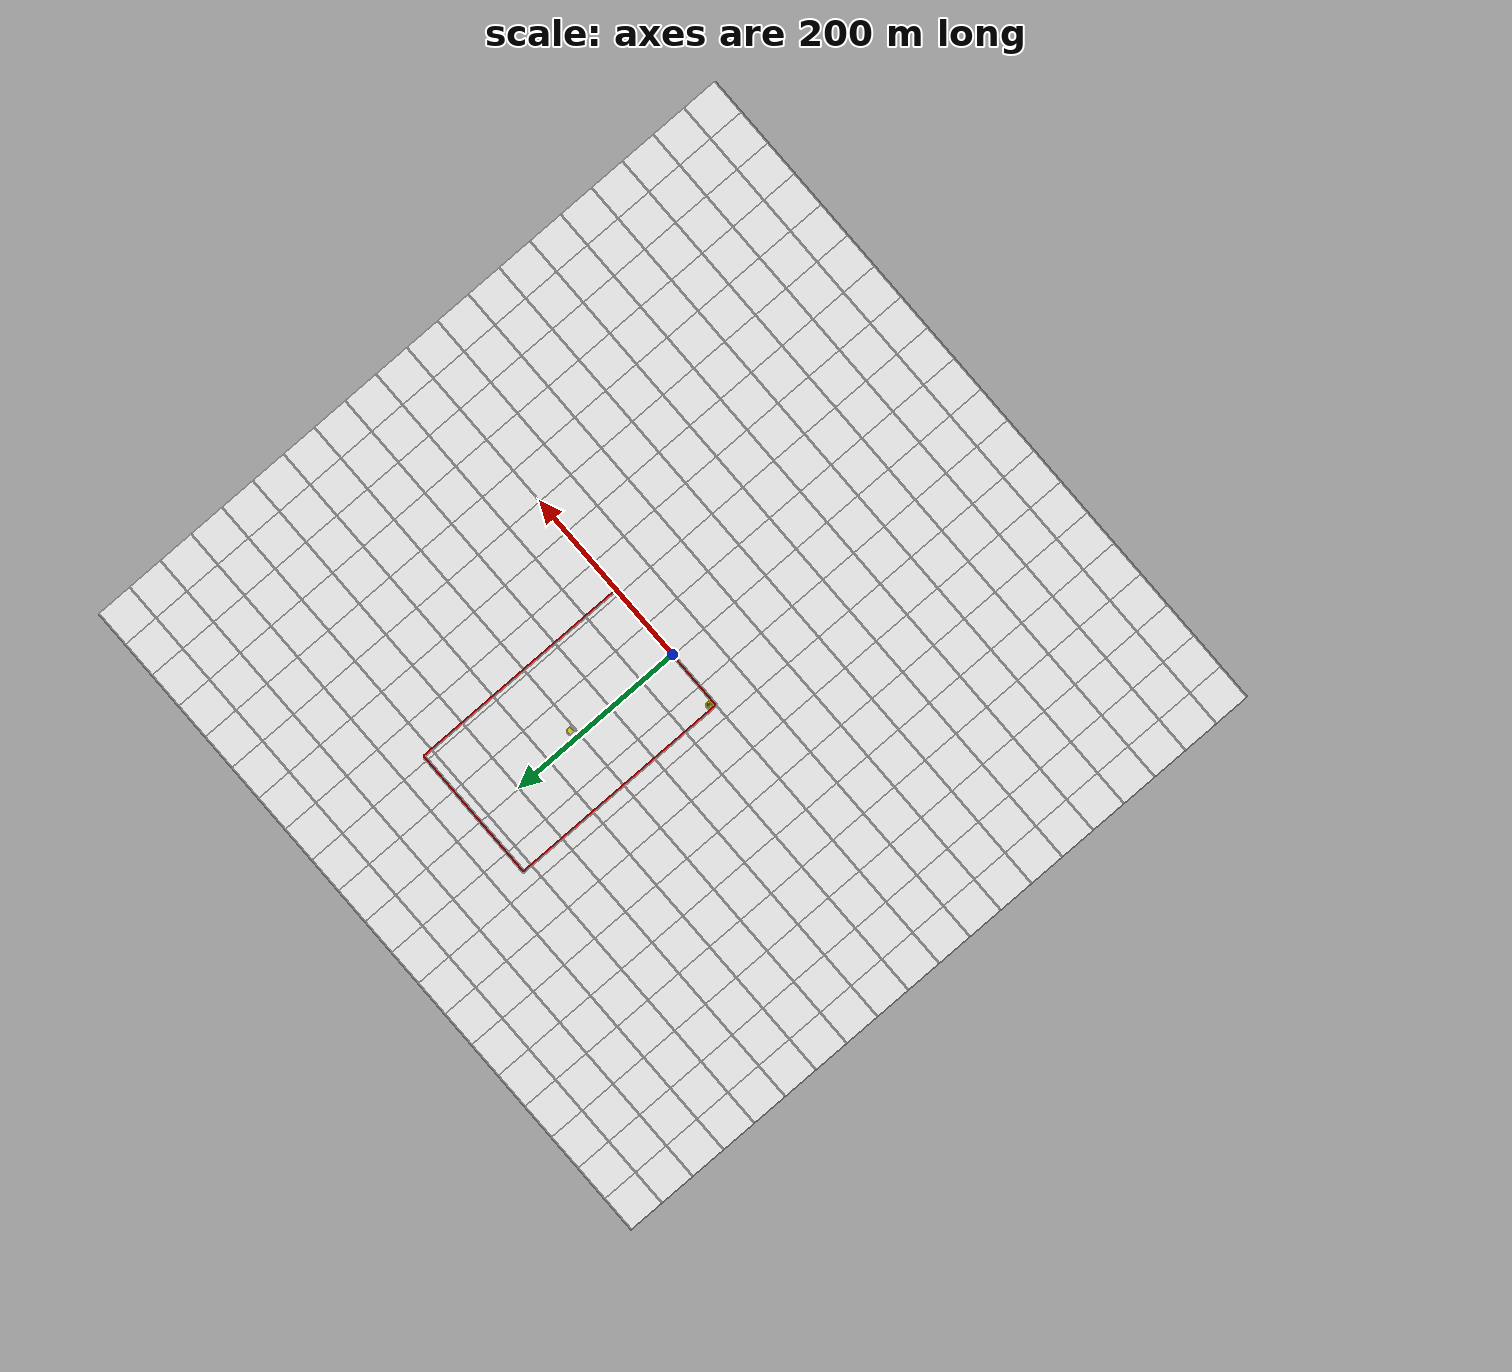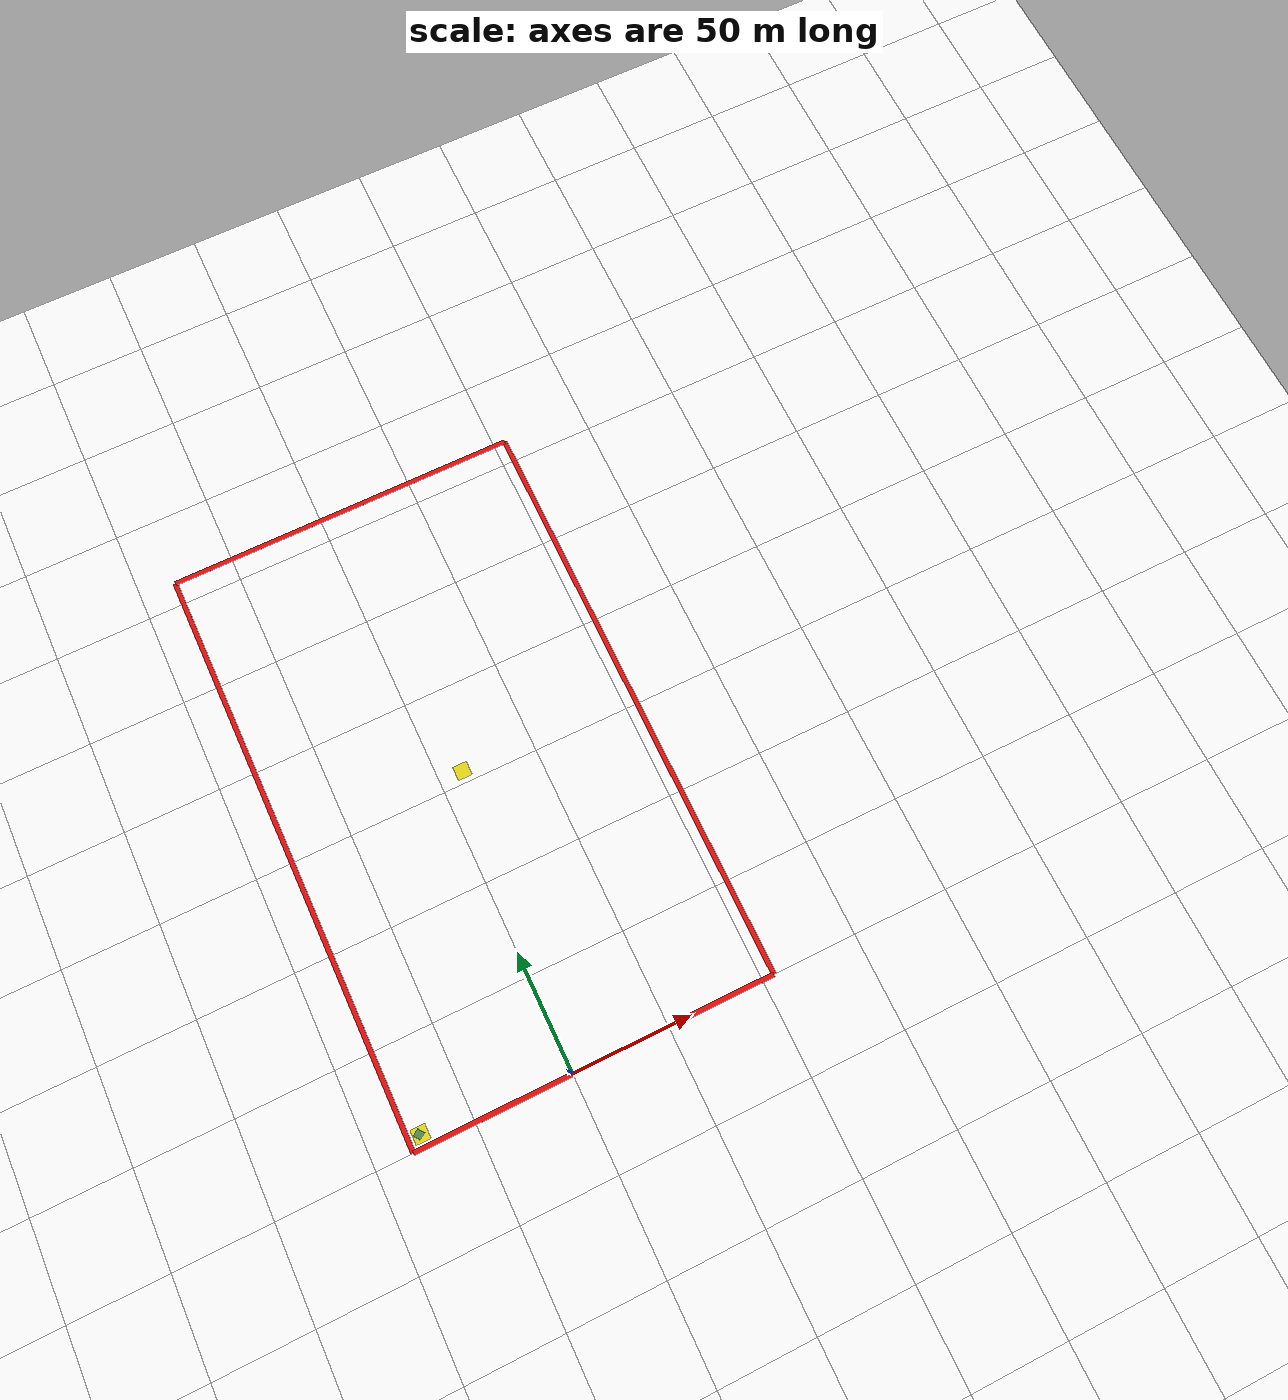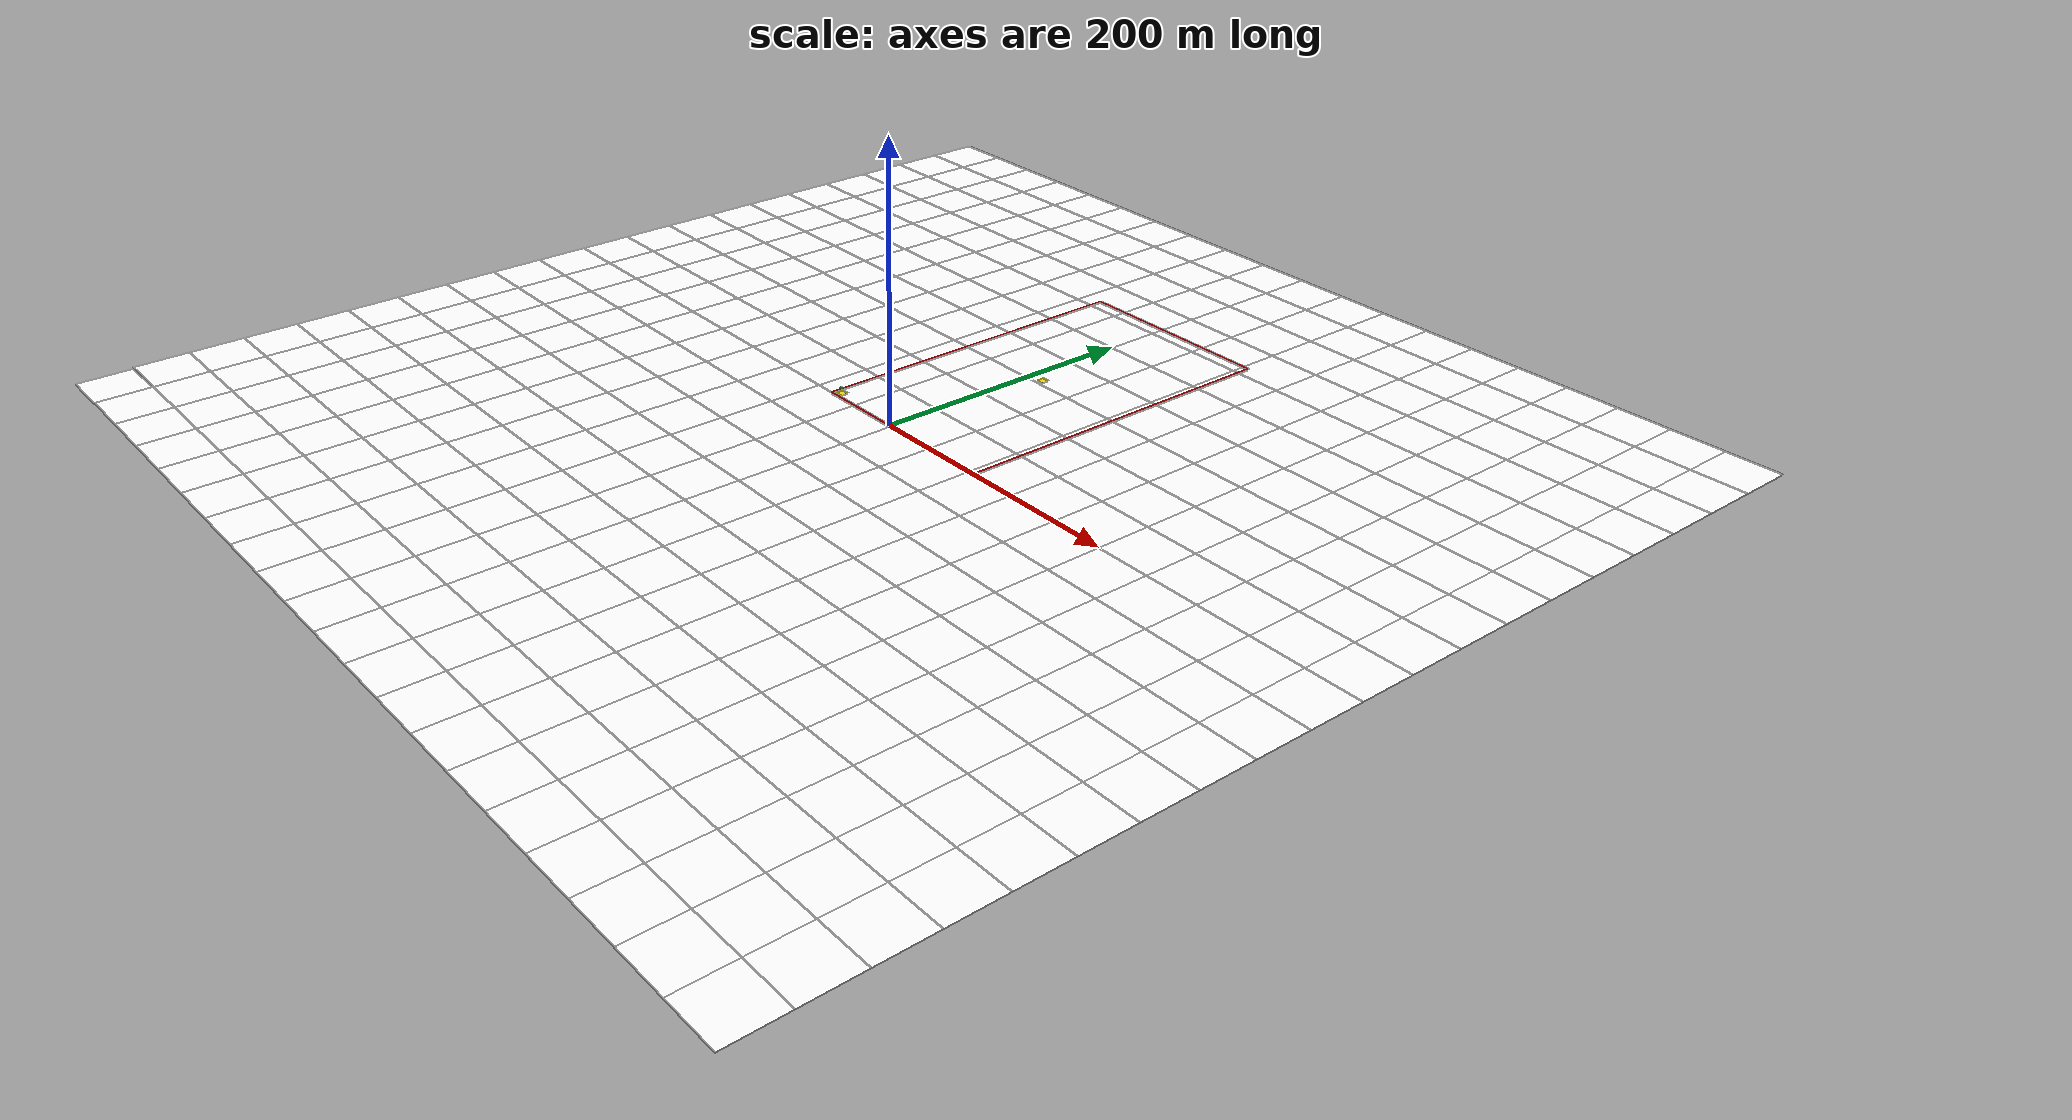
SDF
<sdf version="1.9">
 <world name="suas_field">
  <physics type="ode">
   <max_step_size>0.001</max_step_size>
   <real_time_factor>1.0</real_time_factor>
   <real_time_update_rate>1000</real_time_update_rate>
  </physics>
  <plugin filename="gz-sim-physics-system" name="gz::sim::systems::Physics"/>
  <plugin filename="gz-sim-sensors-system" name="gz::sim::systems::Sensors">
   <render_engine>ogre2</render_engine>
  </plugin>
  <plugin filename="gz-sim-user-commands-system" name="gz::sim::systems::UserCommands"/>
  <plugin filename="gz-sim-scene-broadcaster-system" name="gz::sim::systems::SceneBroadcaster"/>
  <plugin filename="gz-sim-imu-system" name="gz::sim::systems::Imu"/>
  <gravity>0 0 -9.8</gravity>
  <magnetic_field>6e-06 2.3e-05 -4.2e-05</magnetic_field>
  <atmosphere type="adiabatic"/>
  <scene>
   <grid>false</grid>
   <ambient>0.4 0.4 0.4 1</ambient>
   <background>0.7 0.7 0.7 1</background>
   <shadows>false</shadows>
  </scene>
  <include><uri>model://grass_ground_huge</uri></include>
  <light name="sunUTC" type="directional">
   <pose>0 0 500 0 -0 0</pose>
   <cast_shadows>false</cast_shadows>
   <intensity>1</intensity>
   <direction>0.001 0.625 -0.78</direction>
   <diffuse>0.904 0.904 0.904 1</diffuse>
   <specular>0.271 0.271 0.271 1</specular>
  </light>
  <spherical_coordinates>
   <surface_model>EARTH_WGS84</surface_model>
   <world_frame_orientation>ENU</world_frame_orientation>
   <latitude_deg>47.397971057728974</latitude_deg>
   <longitude_deg>8.546163739800146</longitude_deg>
   <elevation>0</elevation>
  </spherical_coordinates>
  <model name="granica_S">
   <static>true</static>
   <pose>10 0 0.02 0 0 0</pose>
   <link name="l">
    <visual name="v">
     <geometry><box><size>150 2 0.02</size></box></geometry>
     <material>
      <ambient>0.9 0.05 0.05 1</ambient>
      <diffuse>0.9 0.05 0.05 1</diffuse>
      <emissive>0.35 0 0 1</emissive>
     </material>
    </visual>
   </link>
  </model>
  <model name="granica_N">
   <static>true</static>
   <pose>10 250 0.02 0 0 0</pose>
   <link name="l">
    <visual name="v">
     <geometry><box><size>150 2 0.02</size></box></geometry>
     <material>
      <ambient>0.9 0.05 0.05 1</ambient>
      <diffuse>0.9 0.05 0.05 1</diffuse>
      <emissive>0.35 0 0 1</emissive>
     </material>
    </visual>
   </link>
  </model>
  <model name="granica_W">
   <static>true</static>
   <pose>-65 125 0.02 0 0 0</pose>
   <link name="l">
    <visual name="v">
     <geometry><box><size>2 250 0.02</size></box></geometry>
     <material>
      <ambient>0.9 0.05 0.05 1</ambient>
      <diffuse>0.9 0.05 0.05 1</diffuse>
      <emissive>0.35 0 0 1</emissive>
     </material>
    </visual>
   </link>
  </model>
  <model name="granica_E">
   <static>true</static>
   <pose>85 125 0.02 0 0 0</pose>
   <link name="l">
    <visual name="v">
     <geometry><box><size>2 250 0.02</size></box></geometry>
     <material>
      <ambient>0.9 0.05 0.05 1</ambient>
      <diffuse>0.9 0.05 0.05 1</diffuse>
      <emissive>0.35 0 0 1</emissive>
     </material>
    </visual>
   </link>
  </model>
  <model name="wp1_marker">
   <static>true</static>
   <pose>-60 5 0.03 0 0 0</pose>
   <link name="l">
    <visual name="v">
     <geometry><box><size>6 6 0.02</size></box></geometry>
     <material>
      <ambient>0.9 0.85 0.1 1</ambient>
      <diffuse>0.9 0.85 0.1 1</diffuse>
      <emissive>0.35 0.32 0 1</emissive>
     </material>
    </visual>
   </link>
  </model>
  <model name="wp2_marker">
   <static>true</static>
   <pose>10 125 0.03 0 0 0</pose>
   <link name="l">
    <visual name="v">
     <geometry><box><size>6 6 0.02</size></box></geometry>
     <material>
      <ambient>0.9 0.85 0.1 1</ambient>
      <diffuse>0.9 0.85 0.1 1</diffuse>
      <emissive>0.35 0.32 0 1</emissive>
     </material>
    </visual>
   </link>
  </model>
  <include>
   <name>tent_target</name>
   <pose>-60 5 0.55 0 0 0.6</pose>
   <uri>model://tent_green</uri>
   <static>true</static>
  </include>
 </world>
</sdf>

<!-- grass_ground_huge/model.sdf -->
<sdf version="1.9">
  <model name="grass_ground_huge">
    <static>true</static>
    <link name="link">
      <collision name="collision">
        <geometry>
          <plane>
            <normal>0 0 1</normal>
            <size>800 800</size>
          </plane>
        </geometry>
      </collision>
      <!-- Siatka kafli 40x40 m -->
      <visual name="tile_0_0"><pose>-380 -380 0 0 0 0</pose><cast_shadows>false</cast_shadows><geometry><plane><normal>0 0 1</normal><size>40 40</size></plane></geometry><material><diffuse>1 1 1 1</diffuse><ambient>1 1 1 1</ambient><pbr><metal><albedo_map>materials/textures/grass_dry.png</albedo_map></metal></pbr></material></visual>
      <visual name="tile_1_0"><pose>-340 -380 0 0 0 0</pose><cast_shadows>false</cast_shadows><geometry><plane><normal>0 0 1</normal><size>40 40</size></plane></geometry><material><diffuse>1 1 1 1</diffuse><ambient>1 1 1 1</ambient><pbr><metal><albedo_map>materials/textures/grass_dry.png</albedo_map></metal></pbr></material></visual>
      <visual name="tile_2_0"><pose>-300 -380 0 0 0 0</pose><cast_shadows>false</cast_shadows><geometry><plane><normal>0 0 1</normal><size>40 40</size></plane></geometry><material><diffuse>1 1 1 1</diffuse><ambient>1 1 1 1</ambient><pbr><metal><albedo_map>materials/textures/grass_dry.png</albedo_map></metal></pbr></material></visual>
      <visual name="tile_3_0"><pose>-260 -380 0 0 0 0</pose><cast_shadows>false</cast_shadows><geometry><plane><normal>0 0 1</normal><size>40 40</size></plane></geometry><material><diffuse>1 1 1 1</diffuse><ambient>1 1 1 1</ambient><pbr><metal><albedo_map>materials/textures/grass_dry.png</albedo_map></metal></pbr></material></visual>
      <visual name="tile_4_0"><pose>-220 -380 0 0 0 0</pose><cast_shadows>false</cast_shadows><geometry><plane><normal>0 0 1</normal><size>40 40</size></plane></geometry><material><diffuse>1 1 1 1</diffuse><ambient>1 1 1 1</ambient><pbr><metal><albedo_map>materials/textures/grass_dry.png</albedo_map></metal></pbr></material></visual>
      <visual name="tile_5_0"><pose>-180 -380 0 0 0 0</pose><cast_shadows>false</cast_shadows><geometry><plane><normal>0 0 1</normal><size>40 40</size></plane></geometry><material><diffuse>1 1 1 1</diffuse><ambient>1 1 1 1</ambient><pbr><metal><albedo_map>materials/textures/grass_dry.png</albedo_map></metal></pbr></material></visual>
      <visual name="tile_6_0"><pose>-140 -380 0 0 0 0</pose><cast_shadows>false</cast_shadows><geometry><plane><normal>0 0 1</normal><size>40 40</size></plane></geometry><material><diffuse>1 1 1 1</diffuse><ambient>1 1 1 1</ambient><pbr><metal><albedo_map>materials/textures/grass_dry.png</albedo_map></metal></pbr></material></visual>
      <visual name="tile_7_0"><pose>-100 -380 0 0 0 0</pose><cast_shadows>false</cast_shadows><geometry><plane><normal>0 0 1</normal><size>40 40</size></plane></geometry><material><diffuse>1 1 1 1</diffuse><ambient>1 1 1 1</ambient><pbr><metal><albedo_map>materials/textures/grass_dry.png</albedo_map></metal></pbr></material></visual>
      <visual name="tile_8_0"><pose>-60 -380 0 0 0 0</pose><cast_shadows>false</cast_shadows><geometry><plane><normal>0 0 1</normal><size>40 40</size></plane></geometry><material><diffuse>1 1 1 1</diffuse><ambient>1 1 1 1</ambient><pbr><metal><albedo_map>materials/textures/grass_dry.png</albedo_map></metal></pbr></material></visual>
      <visual name="tile_9_0"><pose>-20 -380 0 0 0 0</pose><cast_shadows>false</cast_shadows><geometry><plane><normal>0 0 1</normal><size>40 40</size></plane></geometry><material><diffuse>1 1 1 1</diffuse><ambient>1 1 1 1</ambient><pbr><metal><albedo_map>materials/textures/grass_dry.png</albedo_map></metal></pbr></material></visual>
      <visual name="tile_10_0"><pose>20 -380 0 0 0 0</pose><cast_shadows>false</cast_shadows><geometry><plane><normal>0 0 1</normal><size>40 40</size></plane></geometry><material><diffuse>1 1 1 1</diffuse><ambient>1 1 1 1</ambient><pbr><metal><albedo_map>materials/textures/grass_dry.png</albedo_map></metal></pbr></material></visual>
      <visual name="tile_11_0"><pose>60 -380 0 0 0 0</pose><cast_shadows>false</cast_shadows><geometry><plane><normal>0 0 1</normal><size>40 40</size></plane></geometry><material><diffuse>1 1 1 1</diffuse><ambient>1 1 1 1</ambient><pbr><metal><albedo_map>materials/textures/grass_dry.png</albedo_map></metal></pbr></material></visual>
      <visual name="tile_12_0"><pose>100 -380 0 0 0 0</pose><cast_shadows>false</cast_shadows><geometry><plane><normal>0 0 1</normal><size>40 40</size></plane></geometry><material><diffuse>1 1 1 1</diffuse><ambient>1 1 1 1</ambient><pbr><metal><albedo_map>materials/textures/grass_dry.png</albedo_map></metal></pbr></material></visual>
      <visual name="tile_13_0"><pose>140 -380 0 0 0 0</pose><cast_shadows>false</cast_shadows><geometry><plane><normal>0 0 1</normal><size>40 40</size></plane></geometry><material><diffuse>1 1 1 1</diffuse><ambient>1 1 1 1</ambient><pbr><metal><albedo_map>materials/textures/grass_dry.png</albedo_map></metal></pbr></material></visual>
      <visual name="tile_14_0"><pose>180 -380 0 0 0 0</pose><cast_shadows>false</cast_shadows><geometry><plane><normal>0 0 1</normal><size>40 40</size></plane></geometry><material><diffuse>1 1 1 1</diffuse><ambient>1 1 1 1</ambient><pbr><metal><albedo_map>materials/textures/grass_dry.png</albedo_map></metal></pbr></material></visual>
      <visual name="tile_15_0"><pose>220 -380 0 0 0 0</pose><cast_shadows>false</cast_shadows><geometry><plane><normal>0 0 1</normal><size>40 40</size></plane></geometry><material><diffuse>1 1 1 1</diffuse><ambient>1 1 1 1</ambient><pbr><metal><albedo_map>materials/textures/grass_dry.png</albedo_map></metal></pbr></material></visual>
      <visual name="tile_16_0"><pose>260 -380 0 0 0 0</pose><cast_shadows>false</cast_shadows><geometry><plane><normal>0 0 1</normal><size>40 40</size></plane></geometry><material><diffuse>1 1 1 1</diffuse><ambient>1 1 1 1</ambient><pbr><metal><albedo_map>materials/textures/grass_dry.png</albedo_map></metal></pbr></material></visual>
      <visual name="tile_17_0"><pose>300 -380 0 0 0 0</pose><cast_shadows>false</cast_shadows><geometry><plane><normal>0 0 1</normal><size>40 40</size></plane></geometry><material><diffuse>1 1 1 1</diffuse><ambient>1 1 1 1</ambient><pbr><metal><albedo_map>materials/textures/grass_dry.png</albedo_map></metal></pbr></material></visual>
      <visual name="tile_18_0"><pose>340 -380 0 0 0 0</pose><cast_shadows>false</cast_shadows><geometry><plane><normal>0 0 1</normal><size>40 40</size></plane></geometry><material><diffuse>1 1 1 1</diffuse><ambient>1 1 1 1</ambient><pbr><metal><albedo_map>materials/textures/grass_dry.png</albedo_map></metal></pbr></material></visual>
      <visual name="tile_19_0"><pose>380 -380 0 0 0 0</pose><cast_shadows>false</cast_shadows><geometry><plane><normal>0 0 1</normal><size>40 40</size></plane></geometry><material><diffuse>1 1 1 1</diffuse><ambient>1 1 1 1</ambient><pbr><metal><albedo_map>materials/textures/grass_dry.png</albedo_map></metal></pbr></material></visual>
      <visual name="tile_0_1"><pose>-380 -340 0 0 0 0</pose><cast_shadows>false</cast_shadows><geometry><plane><normal>0 0 1</normal><size>40 40</size></plane></geometry><material><diffuse>1 1 1 1</diffuse><ambient>1 1 1 1</ambient><pbr><metal><albedo_map>materials/textures/grass_dry.png</albedo_map></metal></pbr></material></visual>
      <visual name="tile_1_1"><pose>-340 -340 0 0 0 0</pose><cast_shadows>false</cast_shadows><geometry><plane><normal>0 0 1</normal><size>40 40</size></plane></geometry><material><diffuse>1 1 1 1</diffuse><ambient>1 1 1 1</ambient><pbr><metal><albedo_map>materials/textures/grass_dry.png</albedo_map></metal></pbr></material></visual>
      <visual name="tile_2_1"><pose>-300 -340 0 0 0 0</pose><cast_shadows>false</cast_shadows><geometry><plane><normal>0 0 1</normal><size>40 40</size></plane></geometry><material><diffuse>1 1 1 1</diffuse><ambient>1 1 1 1</ambient><pbr><metal><albedo_map>materials/textures/grass_dry.png</albedo_map></metal></pbr></material></visual>
      <visual name="tile_3_1"><pose>-260 -340 0 0 0 0</pose><cast_shadows>false</cast_shadows><geometry><plane><normal>0 0 1</normal><size>40 40</size></plane></geometry><material><diffuse>1 1 1 1</diffuse><ambient>1 1 1 1</ambient><pbr><metal><albedo_map>materials/textures/grass_dry.png</albedo_map></metal></pbr></material></visual>
      <visual name="tile_4_1"><pose>-220 -340 0 0 0 0</pose><cast_shadows>false</cast_shadows><geometry><plane><normal>0 0 1</normal><size>40 40</size></plane></geometry><material><diffuse>1 1 1 1</diffuse><ambient>1 1 1 1</ambient><pbr><metal><albedo_map>materials/textures/grass_dry.png</albedo_map></metal></pbr></material></visual>
      <visual name="tile_5_1"><pose>-180 -340 0 0 0 0</pose><cast_shadows>false</cast_shadows><geometry><plane><normal>0 0 1</normal><size>40 40</size></plane></geometry><material><diffuse>1 1 1 1</diffuse><ambient>1 1 1 1</ambient><pbr><metal><albedo_map>materials/textures/grass_dry.png</albedo_map></metal></pbr></material></visual>
      <visual name="tile_6_1"><pose>-140 -340 0 0 0 0</pose><cast_shadows>false</cast_shadows><geometry><plane><normal>0 0 1</normal><size>40 40</size></plane></geometry><material><diffuse>1 1 1 1</diffuse><ambient>1 1 1 1</ambient><pbr><metal><albedo_map>materials/textures/grass_dry.png</albedo_map></metal></pbr></material></visual>
      <visual name="tile_7_1"><pose>-100 -340 0 0 0 0</pose><cast_shadows>false</cast_shadows><geometry><plane><normal>0 0 1</normal><size>40 40</size></plane></geometry><material><diffuse>1 1 1 1</diffuse><ambient>1 1 1 1</ambient><pbr><metal><albedo_map>materials/textures/grass_dry.png</albedo_map></metal></pbr></material></visual>
      <visual name="tile_8_1"><pose>-60 -340 0 0 0 0</pose><cast_shadows>false</cast_shadows><geometry><plane><normal>0 0 1</normal><size>40 40</size></plane></geometry><material><diffuse>1 1 1 1</diffuse><ambient>1 1 1 1</ambient><pbr><metal><albedo_map>materials/textures/grass_dry.png</albedo_map></metal></pbr></material></visual>
      <visual name="tile_9_1"><pose>-20 -340 0 0 0 0</pose><cast_shadows>false</cast_shadows><geometry><plane><normal>0 0 1</normal><size>40 40</size></plane></geometry><material><diffuse>1 1 1 1</diffuse><ambient>1 1 1 1</ambient><pbr><metal><albedo_map>materials/textures/grass_dry.png</albedo_map></metal></pbr></material></visual>
      <visual name="tile_10_1"><pose>20 -340 0 0 0 0</pose><cast_shadows>false</cast_shadows><geometry><plane><normal>0 0 1</normal><size>40 40</size></plane></geometry><material><diffuse>1 1 1 1</diffuse><ambient>1 1 1 1</ambient><pbr><metal><albedo_map>materials/textures/grass_dry.png</albedo_map></metal></pbr></material></visual>
      <visual name="tile_11_1"><pose>60 -340 0 0 0 0</pose><cast_shadows>false</cast_shadows><geometry><plane><normal>0 0 1</normal><size>40 40</size></plane></geometry><material><diffuse>1 1 1 1</diffuse><ambient>1 1 1 1</ambient><pbr><metal><albedo_map>materials/textures/grass_dry.png</albedo_map></metal></pbr></material></visual>
      <visual name="tile_12_1"><pose>100 -340 0 0 0 0</pose><cast_shadows>false</cast_shadows><geometry><plane><normal>0 0 1</normal><size>40 40</size></plane></geometry><material><diffuse>1 1 1 1</diffuse><ambient>1 1 1 1</ambient><pbr><metal><albedo_map>materials/textures/grass_dry.png</albedo_map></metal></pbr></material></visual>
      <visual name="tile_13_1"><pose>140 -340 0 0 0 0</pose><cast_shadows>false</cast_shadows><geometry><plane><normal>0 0 1</normal><size>40 40</size></plane></geometry><material><diffuse>1 1 1 1</diffuse><ambient>1 1 1 1</ambient><pbr><metal><albedo_map>materials/textures/grass_dry.png</albedo_map></metal></pbr></material></visual>
      <visual name="tile_14_1"><pose>180 -340 0 0 0 0</pose><cast_shadows>false</cast_shadows><geometry><plane><normal>0 0 1</normal><size>40 40</size></plane></geometry><material><diffuse>1 1 1 1</diffuse><ambient>1 1 1 1</ambient><pbr><metal><albedo_map>materials/textures/grass_dry.png</albedo_map></metal></pbr></material></visual>
      <visual name="tile_15_1"><pose>220 -340 0 0 0 0</pose><cast_shadows>false</cast_shadows><geometry><plane><normal>0 0 1</normal><size>40 40</size></plane></geometry><material><diffuse>1 1 1 1</diffuse><ambient>1 1 1 1</ambient><pbr><metal><albedo_map>materials/textures/grass_dry.png</albedo_map></metal></pbr></material></visual>
      <visual name="tile_16_1"><pose>260 -340 0 0 0 0</pose><cast_shadows>false</cast_shadows><geometry><plane><normal>0 0 1</normal><size>40 40</size></plane></geometry><material><diffuse>1 1 1 1</diffuse><ambient>1 1 1 1</ambient><pbr><metal><albedo_map>materials/textures/grass_dry.png</albedo_map></metal></pbr></material></visual>
      <visual name="tile_17_1"><pose>300 -340 0 0 0 0</pose><cast_shadows>false</cast_shadows><geometry><plane><normal>0 0 1</normal><size>40 40</size></plane></geometry><material><diffuse>1 1 1 1</diffuse><ambient>1 1 1 1</ambient><pbr><metal><albedo_map>materials/textures/grass_dry.png</albedo_map></metal></pbr></material></visual>
      <visual name="tile_18_1"><pose>340 -340 0 0 0 0</pose><cast_shadows>false</cast_shadows><geometry><plane><normal>0 0 1</normal><size>40 40</size></plane></geometry><material><diffuse>1 1 1 1</diffuse><ambient>1 1 1 1</ambient><pbr><metal><albedo_map>materials/textures/grass_dry.png</albedo_map></metal></pbr></material></visual>
      <visual name="tile_19_1"><pose>380 -340 0 0 0 0</pose><cast_shadows>false</cast_shadows><geometry><plane><normal>0 0 1</normal><size>40 40</size></plane></geometry><material><diffuse>1 1 1 1</diffuse><ambient>1 1 1 1</ambient><pbr><metal><albedo_map>materials/textures/grass_dry.png</albedo_map></metal></pbr></material></visual>
      <visual name="tile_0_2"><pose>-380 -300 0 0 0 0</pose><cast_shadows>false</cast_shadows><geometry><plane><normal>0 0 1</normal><size>40 40</size></plane></geometry><material><diffuse>1 1 1 1</diffuse><ambient>1 1 1 1</ambient><pbr><metal><albedo_map>materials/textures/grass_dry.png</albedo_map></metal></pbr></material></visual>
      <visual name="tile_1_2"><pose>-340 -300 0 0 0 0</pose><cast_shadows>false</cast_shadows><geometry><plane><normal>0 0 1</normal><size>40 40</size></plane></geometry><material><diffuse>1 1 1 1</diffuse><ambient>1 1 1 1</ambient><pbr><metal><albedo_map>materials/textures/grass_dry.png</albedo_map></metal></pbr></material></visual>
      <visual name="tile_2_2"><pose>-300 -300 0 0 0 0</pose><cast_shadows>false</cast_shadows><geometry><plane><normal>0 0 1</normal><size>40 40</size></plane></geometry><material><diffuse>1 1 1 1</diffuse><ambient>1 1 1 1</ambient><pbr><metal><albedo_map>materials/textures/grass_dry.png</albedo_map></metal></pbr></material></visual>
      <visual name="tile_3_2"><pose>-260 -300 0 0 0 0</pose><cast_shadows>false</cast_shadows><geometry><plane><normal>0 0 1</normal><size>40 40</size></plane></geometry><material><diffuse>1 1 1 1</diffuse><ambient>1 1 1 1</ambient><pbr><metal><albedo_map>materials/textures/grass_dry.png</albedo_map></metal></pbr></material></visual>
      <visual name="tile_4_2"><pose>-220 -300 0 0 0 0</pose><cast_shadows>false</cast_shadows><geometry><plane><normal>0 0 1</normal><size>40 40</size></plane></geometry><material><diffuse>1 1 1 1</diffuse><ambient>1 1 1 1</ambient><pbr><metal><albedo_map>materials/textures/grass_dry.png</albedo_map></metal></pbr></material></visual>
      <visual name="tile_5_2"><pose>-180 -300 0 0 0 0</pose><cast_shadows>false</cast_shadows><geometry><plane><normal>0 0 1</normal><size>40 40</size></plane></geometry><material><diffuse>1 1 1 1</diffuse><ambient>1 1 1 1</ambient><pbr><metal><albedo_map>materials/textures/grass_dry.png</albedo_map></metal></pbr></material></visual>
      <visual name="tile_6_2"><pose>-140 -300 0 0 0 0</pose><cast_shadows>false</cast_shadows><geometry><plane><normal>0 0 1</normal><size>40 40</size></plane></geometry><material><diffuse>1 1 1 1</diffuse><ambient>1 1 1 1</ambient><pbr><metal><albedo_map>materials/textures/grass_dry.png</albedo_map></metal></pbr></material></visual>
      <visual name="tile_7_2"><pose>-100 -300 0 0 0 0</pose><cast_shadows>false</cast_shadows><geometry><plane><normal>0 0 1</normal><size>40 40</size></plane></geometry><material><diffuse>1 1 1 1</diffuse><ambient>1 1 1 1</ambient><pbr><metal><albedo_map>materials/textures/grass_dry.png</albedo_map></metal></pbr></material></visual>
      <visual name="tile_8_2"><pose>-60 -300 0 0 0 0</pose><cast_shadows>false</cast_shadows><geometry><plane><normal>0 0 1</normal><size>40 40</size></plane></geometry><material><diffuse>1 1 1 1</diffuse><ambient>1 1 1 1</ambient><pbr><metal><albedo_map>materials/textures/grass_dry.png</albedo_map></metal></pbr></material></visual>
      <visual name="tile_9_2"><pose>-20 -300 0 0 0 0</pose><cast_shadows>false</cast_shadows><geometry><plane><normal>0 0 1</normal><size>40 40</size></plane></geometry><material><diffuse>1 1 1 1</diffuse><ambient>1 1 1 1</ambient><pbr><metal><albedo_map>materials/textures/grass_dry.png</albedo_map></metal></pbr></material></visual>
      <visual name="tile_10_2"><pose>20 -300 0 0 0 0</pose><cast_shadows>false</cast_shadows><geometry><plane><normal>0 0 1</normal><size>40 40</size></plane></geometry><material><diffuse>1 1 1 1</diffuse><ambient>1 1 1 1</ambient><pbr><metal><albedo_map>materials/textures/grass_dry.png</albedo_map></metal></pbr></material></visual>
      <visual name="tile_11_2"><pose>60 -300 0 0 0 0</pose><cast_shadows>false</cast_shadows><geometry><plane><normal>0 0 1</normal><size>40 40</size></plane></geometry><material><diffuse>1 1 1 1</diffuse><ambient>1 1 1 1</ambient><pbr><metal><albedo_map>materials/textures/grass_dry.png</albedo_map></metal></pbr></material></visual>
      <visual name="tile_12_2"><pose>100 -300 0 0 0 0</pose><cast_shadows>false</cast_shadows><geometry><plane><normal>0 0 1</normal><size>40 40</size></plane></geometry><material><diffuse>1 1 1 1</diffuse><ambient>1 1 1 1</ambient><pbr><metal><albedo_map>materials/textures/grass_dry.png</albedo_map></metal></pbr></material></visual>
      <visual name="tile_13_2"><pose>140 -300 0 0 0 0</pose><cast_shadows>false</cast_shadows><geometry><plane><normal>0 0 1</normal><size>40 40</size></plane></geometry><material><diffuse>1 1 1 1</diffuse><ambient>1 1 1 1</ambient><pbr><metal><albedo_map>materials/textures/grass_dry.png</albedo_map></metal></pbr></material></visual>
      <visual name="tile_14_2"><pose>180 -300 0 0 0 0</pose><cast_shadows>false</cast_shadows><geometry><plane><normal>0 0 1</normal><size>40 40</size></plane></geometry><material><diffuse>1 1 1 1</diffuse><ambient>1 1 1 1</ambient><pbr><metal><albedo_map>materials/textures/grass_dry.png</albedo_map></metal></pbr></material></visual>
      <visual name="tile_15_2"><pose>220 -300 0 0 0 0</pose><cast_shadows>false</cast_shadows><geometry><plane><normal>0 0 1</normal><size>40 40</size></plane></geometry><material><diffuse>1 1 1 1</diffuse><ambient>1 1 1 1</ambient><pbr><metal><albedo_map>materials/textures/grass_dry.png</albedo_map></metal></pbr></material></visual>
      <visual name="tile_16_2"><pose>260 -300 0 0 0 0</pose><cast_shadows>false</cast_shadows><geometry><plane><normal>0 0 1</normal><size>40 40</size></plane></geometry><material><diffuse>1 1 1 1</diffuse><ambient>1 1 1 1</ambient><pbr><metal><albedo_map>materials/textures/grass_dry.png</albedo_map></metal></pbr></material></visual>
      <visual name="tile_17_2"><pose>300 -300 0 0 0 0</pose><cast_shadows>false</cast_shadows><geometry><plane><normal>0 0 1</normal><size>40 40</size></plane></geometry><material><diffuse>1 1 1 1</diffuse><ambient>1 1 1 1</ambient><pbr><metal><albedo_map>materials/textures/grass_dry.png</albedo_map></metal></pbr></material></visual>
      <visual name="tile_18_2"><pose>340 -300 0 0 0 0</pose><cast_shadows>false</cast_shadows><geometry><plane><normal>0 0 1</normal><size>40 40</size></plane></geometry><material><diffuse>1 1 1 1</diffuse><ambient>1 1 1 1</ambient><pbr><metal><albedo_map>materials/textures/grass_dry.png</albedo_map></metal></pbr></material></visual>
      <visual name="tile_19_2"><pose>380 -300 0 0 0 0</pose><cast_shadows>false</cast_shadows><geometry><plane><normal>0 0 1</normal><size>40 40</size></plane></geometry><material><diffuse>1 1 1 1</diffuse><ambient>1 1 1 1</ambient><pbr><metal><albedo_map>materials/textures/grass_dry.png</albedo_map></metal></pbr></material></visual>
      <visual name="tile_0_3"><pose>-380 -260 0 0 0 0</pose><cast_shadows>false</cast_shadows><geometry><plane><normal>0 0 1</normal><size>40 40</size></plane></geometry><material><diffuse>1 1 1 1</diffuse><ambient>1 1 1 1</ambient><pbr><metal><albedo_map>materials/textures/grass_dry.png</albedo_map></metal></pbr></material></visual>
      <visual name="tile_1_3"><pose>-340 -260 0 0 0 0</pose><cast_shadows>false</cast_shadows><geometry><plane><normal>0 0 1</normal><size>40 40</size></plane></geometry><material><diffuse>1 1 1 1</diffuse><ambient>1 1 1 1</ambient><pbr><metal><albedo_map>materials/textures/grass_dry.png</albedo_map></metal></pbr></material></visual>
      <visual name="tile_2_3"><pose>-300 -260 0 0 0 0</pose><cast_shadows>false</cast_shadows><geometry><plane><normal>0 0 1</normal><size>40 40</size></plane></geometry><material><diffuse>1 1 1 1</diffuse><ambient>1 1 1 1</ambient><pbr><metal><albedo_map>materials/textures/grass_dry.png</albedo_map></metal></pbr></material></visual>
      <visual name="tile_3_3"><pose>-260 -260 0 0 0 0</pose><cast_shadows>false</cast_shadows><geometry><plane><normal>0 0 1</normal><size>40 40</size></plane></geometry><material><diffuse>1 1 1 1</diffuse><ambient>1 1 1 1</ambient><pbr><metal><albedo_map>materials/textures/grass_dry.png</albedo_map></metal></pbr></material></visual>
      <visual name="tile_4_3"><pose>-220 -260 0 0 0 0</pose><cast_shadows>false</cast_shadows><geometry><plane><normal>0 0 1</normal><size>40 40</size></plane></geometry><material><diffuse>1 1 1 1</diffuse><ambient>1 1 1 1</ambient><pbr><metal><albedo_map>materials/textures/grass_dry.png</albedo_map></metal></pbr></material></visual>
      <visual name="tile_5_3"><pose>-180 -260 0 0 0 0</pose><cast_shadows>false</cast_shadows><geometry><plane><normal>0 0 1</normal><size>40 40</size></plane></geometry><material><diffuse>1 1 1 1</diffuse><ambient>1 1 1 1</ambient><pbr><metal><albedo_map>materials/textures/grass_dry.png</albedo_map></metal></pbr></material></visual>
      <visual name="tile_6_3"><pose>-140 -260 0 0 0 0</pose><cast_shadows>false</cast_shadows><geometry><plane><normal>0 0 1</normal><size>40 40</size></plane></geometry><material><diffuse>1 1 1 1</diffuse><ambient>1 1 1 1</ambient><pbr><metal><albedo_map>materials/textures/grass_dry.png</albedo_map></metal></pbr></material></visual>
      <visual name="tile_7_3"><pose>-100 -260 0 0 0 0</pose><cast_shadows>false</cast_shadows><geometry><plane><normal>0 0 1</normal><size>40 40</size></plane></geometry><material><diffuse>1 1 1 1</diffuse><ambient>1 1 1 1</ambient><pbr><metal><albedo_map>materials/textures/grass_dry.png</albedo_map></metal></pbr></material></visual>
      <visual name="tile_8_3"><pose>-60 -260 0 0 0 0</pose><cast_shadows>false</cast_shadows><geometry><plane><normal>0 0 1</normal><size>40 40</size></plane></geometry><material><diffuse>1 1 1 1</diffuse><ambient>1 1 1 1</ambient><pbr><metal><albedo_map>materials/textures/grass_dry.png</albedo_map></metal></pbr></material></visual>
      <visual name="tile_9_3"><pose>-20 -260 0 0 0 0</pose><cast_shadows>false</cast_shadows><geometry><plane><normal>0 0 1</normal><size>40 40</size></plane></geometry><material><diffuse>1 1 1 1</diffuse><ambient>1 1 1 1</ambient><pbr><metal><albedo_map>materials/textures/grass_dry.png</albedo_map></metal></pbr></material></visual>
      <visual name="tile_10_3"><pose>20 -260 0 0 0 0</pose><cast_shadows>false</cast_shadows><geometry><plane><normal>0 0 1</normal><size>40 40</size></plane></geometry><material><diffuse>1 1 1 1</diffuse><ambient>1 1 1 1</ambient><pbr><metal><albedo_map>materials/textures/grass_dry.png</albedo_map></metal></pbr></material></visual>
      <visual name="tile_11_3"><pose>60 -260 0 0 0 0</pose><cast_shadows>false</cast_shadows><geometry><plane><normal>0 0 1</normal><size>40 40</size></plane></geometry><material><diffuse>1 1 1 1</diffuse><ambient>1 1 1 1</ambient><pbr><metal><albedo_map>materials/textures/grass_dry.png</albedo_map></metal></pbr></material></visual>
      <visual name="tile_12_3"><pose>100 -260 0 0 0 0</pose><cast_shadows>false</cast_shadows><geometry><plane><normal>0 0 1</normal><size>40 40</size></plane></geometry><material><diffuse>1 1 1 1</diffuse><ambient>1 1 1 1</ambient><pbr><metal><albedo_map>materials/textures/grass_dry.png</albedo_map></metal></pbr></material></visual>
      <visual name="tile_13_3"><pose>140 -260 0 0 0 0</pose><cast_shadows>false</cast_shadows><geometry><plane><normal>0 0 1</normal><size>40 40</size></plane></geometry><material><diffuse>1 1 1 1</diffuse><ambient>1 1 1 1</ambient><pbr><metal><albedo_map>materials/textures/grass_dry.png</albedo_map></metal></pbr></material></visual>
      <visual name="tile_14_3"><pose>180 -260 0 0 0 0</pose><cast_shadows>false</cast_shadows><geometry><plane><normal>0 0 1</normal><size>40 40</size></plane></geometry><material><diffuse>1 1 1 1</diffuse><ambient>1 1 1 1</ambient><pbr><metal><albedo_map>materials/textures/grass_dry.png</albedo_map></metal></pbr></material></visual>
      <visual name="tile_15_3"><pose>220 -260 0 0 0 0</pose><cast_shadows>false</cast_shadows><geometry><plane><normal>0 0 1</normal><size>40 40</size></plane></geometry><material><diffuse>1 1 1 1</diffuse><ambient>1 1 1 1</ambient><pbr><metal><albedo_map>materials/textures/grass_dry.png</albedo_map></metal></pbr></material></visual>
      <visual name="tile_16_3"><pose>260 -260 0 0 0 0</pose><cast_shadows>false</cast_shadows><geometry><plane><normal>0 0 1</normal><size>40 40</size></plane></geometry><material><diffuse>1 1 1 1</diffuse><ambient>1 1 1 1</ambient><pbr><metal><albedo_map>materials/textures/grass_dry.png</albedo_map></metal></pbr></material></visual>
      <visual name="tile_17_3"><pose>300 -260 0 0 0 0</pose><cast_shadows>false</cast_shadows><geometry><plane><normal>0 0 1</normal><size>40 40</size></plane></geometry><material><diffuse>1 1 1 1</diffuse><ambient>1 1 1 1</ambient><pbr><metal><albedo_map>materials/textures/grass_dry.png</albedo_map></metal></pbr></material></visual>
      <visual name="tile_18_3"><pose>340 -260 0 0 0 0</pose><cast_shadows>false</cast_shadows><geometry><plane><normal>0 0 1</normal><size>40 40</size></plane></geometry><material><diffuse>1 1 1 1</diffuse><ambient>1 1 1 1</ambient><pbr><metal><albedo_map>materials/textures/grass_dry.png</albedo_map></metal></pbr></material></visual>
      <visual name="tile_19_3"><pose>380 -260 0 0 0 0</pose><cast_shadows>false</cast_shadows><geometry><plane><normal>0 0 1</normal><size>40 40</size></plane></geometry><material><diffuse>1 1 1 1</diffuse><ambient>1 1 1 1</ambient><pbr><metal><albedo_map>materials/textures/grass_dry.png</albedo_map></metal></pbr></material></visual>
      <visual name="tile_0_4"><pose>-380 -220 0 0 0 0</pose><cast_shadows>false</cast_shadows><geometry><plane><normal>0 0 1</normal><size>40 40</size></plane></geometry><material><diffuse>1 1 1 1</diffuse><ambient>1 1 1 1</ambient><pbr><metal><albedo_map>materials/textures/grass_dry.png</albedo_map></metal></pbr></material></visual>
      <visual name="tile_1_4"><pose>-340 -220 0 0 0 0</pose><cast_shadows>false</cast_shadows><geometry><plane><normal>0 0 1</normal><size>40 40</size></plane></geometry><material><diffuse>1 1 1 1</diffuse><ambient>1 1 1 1</ambient><pbr><metal><albedo_map>materials/textures/grass_dry.png</albedo_map></metal></pbr></material></visual>
      <visual name="tile_2_4"><pose>-300 -220 0 0 0 0</pose><cast_shadows>false</cast_shadows><geometry><plane><normal>0 0 1</normal><size>40 40</size></plane></geometry><material><diffuse>1 1 1 1</diffuse><ambient>1 1 1 1</ambient><pbr><metal><albedo_map>materials/textures/grass_dry.png</albedo_map></metal></pbr></material></visual>
      <visual name="tile_3_4"><pose>-260 -220 0 0 0 0</pose><cast_shadows>false</cast_shadows><geometry><plane><normal>0 0 1</normal><size>40 40</size></plane></geometry><material><diffuse>1 1 1 1</diffuse><ambient>1 1 1 1</ambient><pbr><metal><albedo_map>materials/textures/grass_dry.png</albedo_map></metal></pbr></material></visual>
      <visual name="tile_4_4"><pose>-220 -220 0 0 0 0</pose><cast_shadows>false</cast_shadows><geometry><plane><normal>0 0 1</normal><size>40 40</size></plane></geometry><material><diffuse>1 1 1 1</diffuse><ambient>1 1 1 1</ambient><pbr><metal><albedo_map>materials/textures/grass_dry.png</albedo_map></metal></pbr></material></visual>
      <visual name="tile_5_4"><pose>-180 -220 0 0 0 0</pose><cast_shadows>false</cast_shadows><geometry><plane><normal>0 0 1</normal><size>40 40</size></plane></geometry><material><diffuse>1 1 1 1</diffuse><ambient>1 1 1 1</ambient><pbr><metal><albedo_map>materials/textures/grass_dry.png</albedo_map></metal></pbr></material></visual>
      <visual name="tile_6_4"><pose>-140 -220 0 0 0 0</pose><cast_shadows>false</cast_shadows><geometry><plane><normal>0 0 1</normal><size>40 40</size></plane></geometry><material><diffuse>1 1 1 1</diffuse><ambient>1 1 1 1</ambient><pbr><metal><albedo_map>materials/textures/grass_dry.png</albedo_map></metal></pbr></material></visual>
      <visual name="tile_7_4"><pose>-100 -220 0 0 0 0</pose><cast_shadows>false</cast_shadows><geometry><plane><normal>0 0 1</normal><size>40 40</size></plane></geometry><material><diffuse>1 1 1 1</diffuse><ambient>1 1 1 1</ambient><pbr><metal><albedo_map>materials/textures/grass_dry.png</albedo_map></metal></pbr></material></visual>
      <visual name="tile_8_4"><pose>-60 -220 0 0 0 0</pose><cast_shadows>false</cast_shadows><geometry><plane><normal>0 0 1</normal><size>40 40</size></plane></geometry><material><diffuse>1 1 1 1</diffuse><ambient>1 1 1 1</ambient><pbr><metal><albedo_map>materials/textures/grass_dry.png</albedo_map></metal></pbr></material></visual>
      <visual name="tile_9_4"><pose>-20 -220 0 0 0 0</pose><cast_shadows>false</cast_shadows><geometry><plane><normal>0 0 1</normal><size>40 40</size></plane></geometry><material><diffuse>1 1 1 1</diffuse><ambient>1 1 1 1</ambient><pbr><metal><albedo_map>materials/textures/grass_dry.png</albedo_map></metal></pbr></material></visual>
      <visual name="tile_10_4"><pose>20 -220 0 0 0 0</pose><cast_shadows>false</cast_shadows><geometry><plane><normal>0 0 1</normal><size>40 40</size></plane></geometry><material><diffuse>1 1 1 1</diffuse><ambient>1 1 1 1</ambient><pbr><metal><albedo_map>materials/textures/grass_dry.png</albedo_map></metal></pbr></material></visual>
      <visual name="tile_11_4"><pose>60 -220 0 0 0 0</pose><cast_shadows>false</cast_shadows><geometry><plane><normal>0 0 1</normal><size>40 40</size></plane></geometry><material><diffuse>1 1 1 1</diffuse><ambient>1 1 1 1</ambient><pbr><metal><albedo_map>materials/textures/grass_dry.png</albedo_map></metal></pbr></material></visual>
      <visual name="tile_12_4"><pose>100 -220 0 0 0 0</pose><cast_shadows>false</cast_shadows><geometry><plane><normal>0 0 1</normal><size>40 40</size></plane></geometry><material><diffuse>1 1 1 1</diffuse><ambient>1 1 1 1</ambient><pbr><metal><albedo_map>materials/textures/grass_dry.png</albedo_map></metal></pbr></material></visual>
      <visual name="tile_13_4"><pose>140 -220 0 0 0 0</pose><cast_shadows>false</cast_shadows><geometry><plane><normal>0 0 1</normal><size>40 40</size></plane></geometry><material><diffuse>1 1 1 1</diffuse><ambient>1 1 1 1</ambient><pbr><metal><albedo_map>materials/textures/grass_dry.png</albedo_map></metal></pbr></material></visual>
      <visual name="tile_14_4"><pose>180 -220 0 0 0 0</pose><cast_shadows>false</cast_shadows><geometry><plane><normal>0 0 1</normal><size>40 40</size></plane></geometry><material><diffuse>1 1 1 1</diffuse><ambient>1 1 1 1</ambient><pbr><metal><albedo_map>materials/textures/grass_dry.png</albedo_map></metal></pbr></material></visual>
      <visual name="tile_15_4"><pose>220 -220 0 0 0 0</pose><cast_shadows>false</cast_shadows><geometry><plane><normal>0 0 1</normal><size>40 40</size></plane></geometry><material><diffuse>1 1 1 1</diffuse><ambient>1 1 1 1</ambient><pbr><metal><albedo_map>materials/textures/grass_dry.png</albedo_map></metal></pbr></material></visual>
      <visual name="tile_16_4"><pose>260 -220 0 0 0 0</pose><cast_shadows>false</cast_shadows><geometry><plane><normal>0 0 1</normal><size>40 40</size></plane></geometry><material><diffuse>1 1 1 1</diffuse><ambient>1 1 1 1</ambient><pbr><metal><albedo_map>materials/textures/grass_dry.png</albedo_map></metal></pbr></material></visual>
      <visual name="tile_17_4"><pose>300 -220 0 0 0 0</pose><cast_shadows>false</cast_shadows><geometry><plane><normal>0 0 1</normal><size>40 40</size></plane></geometry><material><diffuse>1 1 1 1</diffuse><ambient>1 1 1 1</ambient><pbr><metal><albedo_map>materials/textures/grass_dry.png</albedo_map></metal></pbr></material></visual>
      <visual name="tile_18_4"><pose>340 -220 0 0 0 0</pose><cast_shadows>false</cast_shadows><geometry><plane><normal>0 0 1</normal><size>40 40</size></plane></geometry><material><diffuse>1 1 1 1</diffuse><ambient>1 1 1 1</ambient><pbr><metal><albedo_map>materials/textures/grass_dry.png</albedo_map></metal></pbr></material></visual>
      <visual name="tile_19_4"><pose>380 -220 0 0 0 0</pose><cast_shadows>false</cast_shadows><geometry><plane><normal>0 0 1</normal><size>40 40</size></plane></geometry><material><diffuse>1 1 1 1</diffuse><ambient>1 1 1 1</ambient><pbr><metal><albedo_map>materials/textures/grass_dry.png</albedo_map></metal></pbr></material></visual>
      <visual name="tile_0_5"><pose>-380 -180 0 0 0 0</pose><cast_shadows>false</cast_shadows><geometry><plane><normal>0 0 1</normal><size>40 40</size></plane></geometry><material><diffuse>1 1 1 1</diffuse><ambient>1 1 1 1</ambient><pbr><metal><albedo_map>materials/textures/grass_dry.png</albedo_map></metal></pbr></material></visual>
      <visual name="tile_1_5"><pose>-340 -180 0 0 0 0</pose><cast_shadows>false</cast_shadows><geometry><plane><normal>0 0 1</normal><size>40 40</size></plane></geometry><material><diffuse>1 1 1 1</diffuse><ambient>1 1 1 1</ambient><pbr><metal><albedo_map>materials/textures/grass_dry.png</albedo_map></metal></pbr></material></visual>
      <visual name="tile_2_5"><pose>-300 -180 0 0 0 0</pose><cast_shadows>false</cast_shadows><geometry><plane><normal>0 0 1</normal><size>40 40</size></plane></geometry><material><diffuse>1 1 1 1</diffuse><ambient>1 1 1 1</ambient><pbr><metal><albedo_map>materials/textures/grass_dry.png</albedo_map></metal></pbr></material></visual>
      <visual name="tile_3_5"><pose>-260 -180 0 0 0 0</pose><cast_shadows>false</cast_shadows><geometry><plane><normal>0 0 1</normal><size>40 40</size></plane></geometry><material><diffuse>1 1 1 1</diffuse><ambient>1 1 1 1</ambient><pbr><metal><albedo_map>materials/textures/grass_dry.png</albedo_map></metal></pbr></material></visual>
      <visual name="tile_4_5"><pose>-220 -180 0 0 0 0</pose><cast_shadows>false</cast_shadows><geometry><plane><normal>0 0 1</normal><size>40 40</size></plane></geometry><material><diffuse>1 1 1 1</diffuse><ambient>1 1 1 1</ambient><pbr><metal><albedo_map>materials/textures/grass_dry.png</albedo_map></metal></pbr></material></visual>
      <visual name="tile_5_5"><pose>-180 -180 0 0 0 0</pose><cast_shadows>false</cast_shadows><geometry><plane><normal>0 0 1</normal><size>40 40</size></plane></geometry><material><diffuse>1 1 1 1</diffuse><ambient>1 1 1 1</ambient><pbr><metal><albedo_map>materials/textures/grass_dry.png</albedo_map></metal></pbr></material></visual>
      <visual name="tile_6_5"><pose>-140 -180 0 0 0 0</pose><cast_shadows>false</cast_shadows><geometry><plane><normal>0 0 1</normal><size>40 40</size></plane></geometry><material><diffuse>1 1 1 1</diffuse><ambient>1 1 1 1</ambient><pbr><metal><albedo_map>materials/textures/grass_dry.png</albedo_map></metal></pbr></material></visual>
      <visual name="tile_7_5"><pose>-100 -180 0 0 0 0</pose><cast_shadows>false</cast_shadows><geometry><plane><normal>0 0 1</normal><size>40 40</size></plane></geometry><material><diffuse>1 1 1 1</diffuse><ambient>1 1 1 1</ambient><pbr><metal><albedo_map>materials/textures/grass_dry.png</albedo_map></metal></pbr></material></visual>
      <visual name="tile_8_5"><pose>-60 -180 0 0 0 0</pose><cast_shadows>false</cast_shadows><geometry><plane><normal>0 0 1</normal><size>40 40</size></plane></geometry><material><diffuse>1 1 1 1</diffuse><ambient>1 1 1 1</ambient><pbr><metal><albedo_map>materials/textures/grass_dry.png</albedo_map></metal></pbr></material></visual>
      <visual name="tile_9_5"><pose>-20 -180 0 0 0 0</pose><cast_shadows>false</cast_shadows><geometry><plane><normal>0 0 1</normal><size>40 40</size></plane></geometry><material><diffuse>1 1 1 1</diffuse><ambient>1 1 1 1</ambient><pbr><metal><albedo_map>materials/textures/grass_dry.png</albedo_map></metal></pbr></material></visual>
      <visual name="tile_10_5"><pose>20 -180 0 0 0 0</pose><cast_shadows>false</cast_shadows><geometry><plane><normal>0 0 1</normal><size>40 40</size></plane></geometry><material><diffuse>1 1 1 1</diffuse><ambient>1 1 1 1</ambient><pbr><metal><albedo_map>materials/textures/grass_dry.png</albedo_map></metal></pbr></material></visual>
      <visual name="tile_11_5"><pose>60 -180 0 0 0 0</pose><cast_shadows>false</cast_shadows><geometry><plane><normal>0 0 1</normal><size>40 40</size></plane></geometry><material><diffuse>1 1 1 1</diffuse><ambient>1 1 1 1</ambient><pbr><metal><albedo_map>materials/textures/grass_dry.png</albedo_map></metal></pbr></material></visual>
      <visual name="tile_12_5"><pose>100 -180 0 0 0 0</pose><cast_shadows>false</cast_shadows><geometry><plane><normal>0 0 1</normal><size>40 40</size></plane></geometry><material><diffuse>1 1 1 1</diffuse><ambient>1 1 1 1</ambient><pbr><metal><albedo_map>materials/textures/grass_dry.png</albedo_map></metal></pbr></material></visual>
      <visual name="tile_13_5"><pose>140 -180 0 0 0 0</pose><cast_shadows>false</cast_shadows><geometry><plane><normal>0 0 1</normal><size>40 40</size></plane></geometry><material><diffuse>1 1 1 1</diffuse><ambient>1 1 1 1</ambient><pbr><metal><albedo_map>materials/textures/grass_dry.png</albedo_map></metal></pbr></material></visual>
      <visual name="tile_14_5"><pose>180 -180 0 0 0 0</pose><cast_shadows>false</cast_shadows><geometry><plane><normal>0 0 1</normal><size>40 40</size></plane></geometry><material><diffuse>1 1 1 1</diffuse><ambient>1 1 1 1</ambient><pbr><metal><albedo_map>materials/textures/grass_dry.png</albedo_map></metal></pbr></material></visual>
      <visual name="tile_15_5"><pose>220 -180 0 0 0 0</pose><cast_shadows>false</cast_shadows><geometry><plane><normal>0 0 1</normal><size>40 40</size></plane></geometry><material><diffuse>1 1 1 1</diffuse><ambient>1 1 1 1</ambient><pbr><metal><albedo_map>materials/textures/grass_dry.png</albedo_map></metal></pbr></material></visual>
      <visual name="tile_16_5"><pose>260 -180 0 0 0 0</pose><cast_shadows>false</cast_shadows><geometry><plane><normal>0 0 1</normal><size>40 40</size></plane></geometry><material><diffuse>1 1 1 1</diffuse><ambient>1 1 1 1</ambient><pbr><metal><albedo_map>materials/textures/grass_dry.png</albedo_map></metal></pbr></material></visual>
      <visual name="tile_17_5"><pose>300 -180 0 0 0 0</pose><cast_shadows>false</cast_shadows><geometry><plane><normal>0 0 1</normal><size>40 40</size></plane></geometry><material><diffuse>1 1 1 1</diffuse><ambient>1 1 1 1</ambient><pbr><metal><albedo_map>materials/textures/grass_dry.png</albedo_map></metal></pbr></material></visual>
      <visual name="tile_18_5"><pose>340 -180 0 0 0 0</pose><cast_shadows>false</cast_shadows><geometry><plane><normal>0 0 1</normal><size>40 40</size></plane></geometry><material><diffuse>1 1 1 1</diffuse><ambient>1 1 1 1</ambient><pbr><metal><albedo_map>materials/textures/grass_dry.png</albedo_map></metal></pbr></material></visual>
      <visual name="tile_19_5"><pose>380 -180 0 0 0 0</pose><cast_shadows>false</cast_shadows><geometry><plane><normal>0 0 1</normal><size>40 40</size></plane></geometry><material><diffuse>1 1 1 1</diffuse><ambient>1 1 1 1</ambient><pbr><metal><albedo_map>materials/textures/grass_dry.png</albedo_map></metal></pbr></material></visual>
      <visual name="tile_0_6"><pose>-380 -140 0 0 0 0</pose><cast_shadows>false</cast_shadows><geometry><plane><normal>0 0 1</normal><size>40 40</size></plane></geometry><material><diffuse>1 1 1 1</diffuse><ambient>1 1 1 1</ambient><pbr><metal><albedo_map>materials/textures/grass_dry.png</albedo_map></metal></pbr></material></visual>
      <visual name="tile_1_6"><pose>-340 -140 0 0 0 0</pose><cast_shadows>false</cast_shadows><geometry><plane><normal>0 0 1</normal><size>40 40</size></plane></geometry><material><diffuse>1 1 1 1</diffuse><ambient>1 1 1 1</ambient><pbr><metal><albedo_map>materials/textures/grass_dry.png</albedo_map></metal></pbr></material></visual>
      <visual name="tile_2_6"><pose>-300 -140 0 0 0 0</pose><cast_shadows>false</cast_shadows><geometry><plane><normal>0 0 1</normal><size>40 40</size></plane></geometry><material><diffuse>1 1 1 1</diffuse><ambient>1 1 1 1</ambient><pbr><metal><albedo_map>materials/textures/grass_dry.png</albedo_map></metal></pbr></material></visual>
      <visual name="tile_3_6"><pose>-260 -140 0 0 0 0</pose><cast_shadows>false</cast_shadows><geometry><plane><normal>0 0 1</normal><size>40 40</size></plane></geometry><material><diffuse>1 1 1 1</diffuse><ambient>1 1 1 1</ambient><pbr><metal><albedo_map>materials/textures/grass_dry.png</albedo_map></metal></pbr></material></visual>
      <visual name="tile_4_6"><pose>-220 -140 0 0 0 0</pose><cast_shadows>false</cast_shadows><geometry><plane><normal>0 0 1</normal><size>40 40</size></plane></geometry><material><diffuse>1 1 1 1</diffuse><ambient>1 1 1 1</ambient><pbr><metal><albedo_map>materials/textures/grass_dry.png</albedo_map></metal></pbr></material></visual>
      <visual name="tile_5_6"><pose>-180 -140 0 0 0 0</pose><cast_shadows>false</cast_shadows><geometry><plane><normal>0 0 1</normal><size>40 40</size></plane></geometry><material><diffuse>1 1 1 1</diffuse><ambient>1 1 1 1</ambient><pbr><metal><albedo_map>materials/textures/grass_dry.png</albedo_map></metal></pbr></material></visual>
      <visual name="tile_6_6"><pose>-140 -140 0 0 0 0</pose><cast_shadows>false</cast_shadows><geometry><plane><normal>0 0 1</normal><size>40 40</size></plane></geometry><material><diffuse>1 1 1 1</diffuse><ambient>1 1 1 1</ambient><pbr><metal><albedo_map>materials/textures/grass_dry.png</albedo_map></metal></pbr></material></visual>
      <visual name="tile_7_6"><pose>-100 -140 0 0 0 0</pose><cast_shadows>false</cast_shadows><geometry><plane><normal>0 0 1</normal><size>40 40</size></plane></geometry><material><diffuse>1 1 1 1</diffuse><ambient>1 1 1 1</ambient><pbr><metal><albedo_map>materials/textures/grass_dry.png</albedo_map></metal></pbr></material></visual>
      <visual name="tile_8_6"><pose>-60 -140 0 0 0 0</pose><cast_shadows>false</cast_shadows><geometry><plane><normal>0 0 1</normal><size>40 40</size></plane></geometry><material><diffuse>1 1 1 1</diffuse><ambient>1 1 1 1</ambient><pbr><metal><albedo_map>materials/textures/grass_dry.png</albedo_map></metal></pbr></material></visual>
      <visual name="tile_9_6"><pose>-20 -140 0 0 0 0</pose><cast_shadows>false</cast_shadows><geometry><plane><normal>0 0 1</normal><size>40 40</size></plane></geometry><material><diffuse>1 1 1 1</diffuse><ambient>1 1 1 1</ambient><pbr><metal><albedo_map>materials/textures/grass_dry.png</albedo_map></metal></pbr></material></visual>
      <visual name="tile_10_6"><pose>20 -140 0 0 0 0</pose><cast_shadows>false</cast_shadows><geometry><plane><normal>0 0 1</normal><size>40 40</size></plane></geometry><material><diffuse>1 1 1 1</diffuse><ambient>1 1 1 1</ambient><pbr><metal><albedo_map>materials/textures/grass_dry.png</albedo_map></metal></pbr></material></visual>
      <visual name="tile_11_6"><pose>60 -140 0 0 0 0</pose><cast_shadows>false</cast_shadows><geometry><plane><normal>0 0 1</normal><size>40 40</size></plane></geometry><material><diffuse>1 1 1 1</diffuse><ambient>1 1 1 1</ambient><pbr><metal><albedo_map>materials/textures/grass_dry.png</albedo_map></metal></pbr></material></visual>
      <visual name="tile_12_6"><pose>100 -140 0 0 0 0</pose><cast_shadows>false</cast_shadows><geometry><plane><normal>0 0 1</normal><size>40 40</size></plane></geometry><material><diffuse>1 1 1 1</diffuse><ambient>1 1 1 1</ambient><pbr><metal><albedo_map>materials/textures/grass_dry.png</albedo_map></metal></pbr></material></visual>
      <visual name="tile_13_6"><pose>140 -140 0 0 0 0</pose><cast_shadows>false</cast_shadows><geometry><plane><normal>0 0 1</normal><size>40 40</size></plane></geometry><material><diffuse>1 1 1 1</diffuse><ambient>1 1 1 1</ambient><pbr><metal><albedo_map>materials/textures/grass_dry.png</albedo_map></metal></pbr></material></visual>
      <visual name="tile_14_6"><pose>180 -140 0 0 0 0</pose><cast_shadows>false</cast_shadows><geometry><plane><normal>0 0 1</normal><size>40 40</size></plane></geometry><material><diffuse>1 1 1 1</diffuse><ambient>1 1 1 1</ambient><pbr><metal><albedo_map>materials/textures/grass_dry.png</albedo_map></metal></pbr></material></visual>
      <visual name="tile_15_6"><pose>220 -140 0 0 0 0</pose><cast_shadows>false</cast_shadows><geometry><plane><normal>0 0 1</normal><size>40 40</size></plane></geometry><material><diffuse>1 1 1 1</diffuse><ambient>1 1 1 1</ambient><pbr><metal><albedo_map>materials/textures/grass_dry.png</albedo_map></metal></pbr></material></visual>
      <visual name="tile_16_6"><pose>260 -140 0 0 0 0</pose><cast_shadows>false</cast_shadows><geometry><plane><normal>0 0 1</normal><size>40 40</size></plane></geometry><material><diffuse>1 1 1 1</diffuse><ambient>1 1 1 1</ambient><pbr><metal><albedo_map>materials/textures/grass_dry.png</albedo_map></metal></pbr></material></visual>
      <visual name="tile_17_6"><pose>300 -140 0 0 0 0</pose><cast_shadows>false</cast_shadows><geometry><plane><normal>0 0 1</normal><size>40 40</size></plane></geometry><material><diffuse>1 1 1 1</diffuse><ambient>1 1 1 1</ambient><pbr><metal><albedo_map>materials/textures/grass_dry.png</albedo_map></metal></pbr></material></visual>
      <visual name="tile_18_6"><pose>340 -140 0 0 0 0</pose><cast_shadows>false</cast_shadows><geometry><plane><normal>0 0 1</normal><size>40 40</size></plane></geometry><material><diffuse>1 1 1 1</diffuse><ambient>1 1 1 1</ambient><pbr><metal><albedo_map>materials/textures/grass_dry.png</albedo_map></metal></pbr></material></visual>
      <visual name="tile_19_6"><pose>380 -140 0 0 0 0</pose><cast_shadows>false</cast_shadows><geometry><plane><normal>0 0 1</normal><size>40 40</size></plane></geometry><material><diffuse>1 1 1 1</diffuse><ambient>1 1 1 1</ambient><pbr><metal><albedo_map>materials/textures/grass_dry.png</albedo_map></metal></pbr></material></visual>
      <visual name="tile_0_7"><pose>-380 -100 0 0 0 0</pose><cast_shadows>false</cast_shadows><geometry><plane><normal>0 0 1</normal><size>40 40</size></plane></geometry><material><diffuse>1 1 1 1</diffuse><ambient>1 1 1 1</ambient><pbr><metal><albedo_map>materials/textures/grass_dry.png</albedo_map></metal></pbr></material></visual>
      <visual name="tile_1_7"><pose>-340 -100 0 0 0 0</pose><cast_shadows>false</cast_shadows><geometry><plane><normal>0 0 1</normal><size>40 40</size></plane></geometry><material><diffuse>1 1 1 1</diffuse><ambient>1 1 1 1</ambient><pbr><metal><albedo_map>materials/textures/grass_dry.png</albedo_map></metal></pbr></material></visual>
      <visual name="tile_2_7"><pose>-300 -100 0 0 0 0</pose><cast_shadows>false</cast_shadows><geometry><plane><normal>0 0 1</normal><size>40 40</size></plane></geometry><material><diffuse>1 1 1 1</diffuse><ambient>1 1 1 1</ambient><pbr><metal><albedo_map>materials/textures/grass_dry.png</albedo_map></metal></pbr></material></visual>
      <visual name="tile_3_7"><pose>-260 -100 0 0 0 0</pose><cast_shadows>false</cast_shadows><geometry><plane><normal>0 0 1</normal><size>40 40</size></plane></geometry><material><diffuse>1 1 1 1</diffuse><ambient>1 1 1 1</ambient><pbr><metal><albedo_map>materials/textures/grass_dry.png</albedo_map></metal></pbr></material></visual>
      <visual name="tile_4_7"><pose>-220 -100 0 0 0 0</pose><cast_shadows>false</cast_shadows><geometry><plane><normal>0 0 1</normal><size>40 40</size></plane></geometry><material><diffuse>1 1 1 1</diffuse><ambient>1 1 1 1</ambient><pbr><metal><albedo_map>materials/textures/grass_dry.png</albedo_map></metal></pbr></material></visual>
      <visual name="tile_5_7"><pose>-180 -100 0 0 0 0</pose><cast_shadows>false</cast_shadows><geometry><plane><normal>0 0 1</normal><size>40 40</size></plane></geometry><material><diffuse>1 1 1 1</diffuse><ambient>1 1 1 1</ambient><pbr><metal><albedo_map>materials/textures/grass_dry.png</albedo_map></metal></pbr></material></visual>
      <visual name="tile_6_7"><pose>-140 -100 0 0 0 0</pose><cast_shadows>false</cast_shadows><geometry><plane><normal>0 0 1</normal><size>40 40</size></plane></geometry><material><diffuse>1 1 1 1</diffuse><ambient>1 1 1 1</ambient><pbr><metal><albedo_map>materials/textures/grass_dry.png</albedo_map></metal></pbr></material></visual>
      <visual name="tile_7_7"><pose>-100 -100 0 0 0 0</pose><cast_shadows>false</cast_shadows><geometry><plane><normal>0 0 1</normal><size>40 40</size></plane></geometry><material><diffuse>1 1 1 1</diffuse><ambient>1 1 1 1</ambient><pbr><metal><albedo_map>materials/textures/grass_dry.png</albedo_map></metal></pbr></material></visual>
      <visual name="tile_8_7"><pose>-60 -100 0 0 0 0</pose><cast_shadows>false</cast_shadows><geometry><plane><normal>0 0 1</normal><size>40 40</size></plane></geometry><material><diffuse>1 1 1 1</diffuse><ambient>1 1 1 1</ambient><pbr><metal><albedo_map>materials/textures/grass_dry.png</albedo_map></metal></pbr></material></visual>
      <visual name="tile_9_7"><pose>-20 -100 0 0 0 0</pose><cast_shadows>false</cast_shadows><geometry><plane><normal>0 0 1</normal><size>40 40</size></plane></geometry><material><diffuse>1 1 1 1</diffuse><ambient>1 1 1 1</ambient><pbr><metal><albedo_map>materials/textures/grass_dry.png</albedo_map></metal></pbr></material></visual>
      <visual name="tile_10_7"><pose>20 -100 0 0 0 0</pose><cast_shadows>false</cast_shadows><geometry><plane><normal>0 0 1</normal><size>40 40</size></plane></geometry><material><diffuse>1 1 1 1</diffuse><ambient>1 1 1 1</ambient><pbr><metal><albedo_map>materials/textures/grass_dry.png</albedo_map></metal></pbr></material></visual>
      <visual name="tile_11_7"><pose>60 -100 0 0 0 0</pose><cast_shadows>false</cast_shadows><geometry><plane><normal>0 0 1</normal><size>40 40</size></plane></geometry><material><diffuse>1 1 1 1</diffuse><ambient>1 1 1 1</ambient><pbr><metal><albedo_map>materials/textures/grass_dry.png</albedo_map></metal></pbr></material></visual>
      <visual name="tile_12_7"><pose>100 -100 0 0 0 0</pose><cast_shadows>false</cast_shadows><geometry><plane><normal>0 0 1</normal><size>40 40</size></plane></geometry><material><diffuse>1 1 1 1</diffuse><ambient>1 1 1 1</ambient><pbr><metal><albedo_map>materials/textures/grass_dry.png</albedo_map></metal></pbr></material></visual>
      <visual name="tile_13_7"><pose>140 -100 0 0 0 0</pose><cast_shadows>false</cast_shadows><geometry><plane><normal>0 0 1</normal><size>40 40</size></plane></geometry><material><diffuse>1 1 1 1</diffuse><ambient>1 1 1 1</ambient><pbr><metal><albedo_map>materials/textures/grass_dry.png</albedo_map></metal></pbr></material></visual>
      <visual name="tile_14_7"><pose>180 -100 0 0 0 0</pose><cast_shadows>false</cast_shadows><geometry><plane><normal>0 0 1</normal><size>40 40</size></plane></geometry><material><diffuse>1 1 1 1</diffuse><ambient>1 1 1 1</ambient><pbr><metal><albedo_map>materials/textures/grass_dry.png</albedo_map></metal></pbr></material></visual>
      <visual name="tile_15_7"><pose>220 -100 0 0 0 0</pose><cast_shadows>false</cast_shadows><geometry><plane><normal>0 0 1</normal><size>40 40</size></plane></geometry><material><diffuse>1 1 1 1</diffuse><ambient>1 1 1 1</ambient><pbr><metal><albedo_map>materials/textures/grass_dry.png</albedo_map></metal></pbr></material></visual>
      <visual name="tile_16_7"><pose>260 -100 0 0 0 0</pose><cast_shadows>false</cast_shadows><geometry><plane><normal>0 0 1</normal><size>40 40</size></plane></geometry><material><diffuse>1 1 1 1</diffuse><ambient>1 1 1 1</ambient><pbr><metal><albedo_map>materials/textures/grass_dry.png</albedo_map></metal></pbr></material></visual>
      <visual name="tile_17_7"><pose>300 -100 0 0 0 0</pose><cast_shadows>false</cast_shadows><geometry><plane><normal>0 0 1</normal><size>40 40</size></plane></geometry><material><diffuse>1 1 1 1</diffuse><ambient>1 1 1 1</ambient><pbr><metal><albedo_map>materials/textures/grass_dry.png</albedo_map></metal></pbr></material></visual>
      <visual name="tile_18_7"><pose>340 -100 0 0 0 0</pose><cast_shadows>false</cast_shadows><geometry><plane><normal>0 0 1</normal><size>40 40</size></plane></geometry><material><diffuse>1 1 1 1</diffuse><ambient>1 1 1 1</ambient><pbr><metal><albedo_map>materials/textures/grass_dry.png</albedo_map></metal></pbr></material></visual>
      <visual name="tile_19_7"><pose>380 -100 0 0 0 0</pose><cast_shadows>false</cast_shadows><geometry><plane><normal>0 0 1</normal><size>40 40</size></plane></geometry><material><diffuse>1 1 1 1</diffuse><ambient>1 1 1 1</ambient><pbr><metal><albedo_map>materials/textures/grass_dry.png</albedo_map></metal></pbr></material></visual>
      <visual name="tile_0_8"><pose>-380 -60 0 0 0 0</pose><cast_shadows>false</cast_shadows><geometry><plane><normal>0 0 1</normal><size>40 40</size></plane></geometry><material><diffuse>1 1 1 1</diffuse><ambient>1 1 1 1</ambient><pbr><metal><albedo_map>materials/textures/grass_dry.png</albedo_map></metal></pbr></material></visual>
      <visual name="tile_1_8"><pose>-340 -60 0 0 0 0</pose><cast_shadows>false</cast_shadows><geometry><plane><normal>0 0 1</normal><size>40 40</size></plane></geometry><material><diffuse>1 1 1 1</diffuse><ambient>1 1 1 1</ambient><pbr><metal><albedo_map>materials/textures/grass_dry.png</albedo_map></metal></pbr></material></visual>
      <visual name="tile_2_8"><pose>-300 -60 0 0 0 0</pose><cast_shadows>false</cast_shadows><geometry><plane><normal>0 0 1</normal><size>40 40</size></plane></geometry><material><diffuse>1 1 1 1</diffuse><ambient>1 1 1 1</ambient><pbr><metal><albedo_map>materials/textures/grass_dry.png</albedo_map></metal></pbr></material></visual>
      <visual name="tile_3_8"><pose>-260 -60 0 0 0 0</pose><cast_shadows>false</cast_shadows><geometry><plane><normal>0 0 1</normal><size>40 40</size></plane></geometry><material><diffuse>1 1 1 1</diffuse><ambient>1 1 1 1</ambient><pbr><metal><albedo_map>materials/textures/grass_dry.png</albedo_map></metal></pbr></material></visual>
      <visual name="tile_4_8"><pose>-220 -60 0 0 0 0</pose><cast_shadows>false</cast_shadows><geometry><plane><normal>0 0 1</normal><size>40 40</size></plane></geometry><material><diffuse>1 1 1 1</diffuse><ambient>1 1 1 1</ambient><pbr><metal><albedo_map>materials/textures/grass_dry.png</albedo_map></metal></pbr></material></visual>
      <visual name="tile_5_8"><pose>-180 -60 0 0 0 0</pose><cast_shadows>false</cast_shadows><geometry><plane><normal>0 0 1</normal><size>40 40</size></plane></geometry><material><diffuse>1 1 1 1</diffuse><ambient>1 1 1 1</ambient><pbr><metal><albedo_map>materials/textures/grass_dry.png</albedo_map></metal></pbr></material></visual>
      <visual name="tile_6_8"><pose>-140 -60 0 0 0 0</pose><cast_shadows>false</cast_shadows><geometry><plane><normal>0 0 1</normal><size>40 40</size></plane></geometry><material><diffuse>1 1 1 1</diffuse><ambient>1 1 1 1</ambient><pbr><metal><albedo_map>materials/textures/grass_dry.png</albedo_map></metal></pbr></material></visual>
      <visual name="tile_7_8"><pose>-100 -60 0 0 0 0</pose><cast_shadows>false</cast_shadows><geometry><plane><normal>0 0 1</normal><size>40 40</size></plane></geometry><material><diffuse>1 1 1 1</diffuse><ambient>1 1 1 1</ambient><pbr><metal><albedo_map>materials/textures/grass_dry.png</albedo_map></metal></pbr></material></visual>
      <visual name="tile_8_8"><pose>-60 -60 0 0 0 0</pose><cast_shadows>false</cast_shadows><geometry><plane><normal>0 0 1</normal><size>40 40</size></plane></geometry><material><diffuse>1 1 1 1</diffuse><ambient>1 1 1 1</ambient><pbr><metal><albedo_map>materials/textures/grass_dry.png</albedo_map></metal></pbr></material></visual>
      <visual name="tile_9_8"><pose>-20 -60 0 0 0 0</pose><cast_shadows>false</cast_shadows><geometry><plane><normal>0 0 1</normal><size>40 40</size></plane></geometry><material><diffuse>1 1 1 1</diffuse><ambient>1 1 1 1</ambient><pbr><metal><albedo_map>materials/textures/grass_dry.png</albedo_map></metal></pbr></material></visual>
      <visual name="tile_10_8"><pose>20 -60 0 0 0 0</pose><cast_shadows>false</cast_shadows><geometry><plane><normal>0 0 1</normal><size>40 40</size></plane></geometry><material><diffuse>1 1 1 1</diffuse><ambient>1 1 1 1</ambient><pbr><metal><albedo_map>materials/textures/grass_dry.png</albedo_map></metal></pbr></material></visual>
      <visual name="tile_11_8"><pose>60 -60 0 0 0 0</pose><cast_shadows>false</cast_shadows><geometry><plane><normal>0 0 1</normal><size>40 40</size></plane></geometry><material><diffuse>1 1 1 1</diffuse><ambient>1 1 1 1</ambient><pbr><metal><albedo_map>materials/textures/grass_dry.png</albedo_map></metal></pbr></material></visual>
      <visual name="tile_12_8"><pose>100 -60 0 0 0 0</pose><cast_shadows>false</cast_shadows><geometry><plane><normal>0 0 1</normal><size>40 40</size></plane></geometry><material><diffuse>1 1 1 1</diffuse><ambient>1 1 1 1</ambient><pbr><metal><albedo_map>materials/textures/grass_dry.png</albedo_map></metal></pbr></material></visual>
      <visual name="tile_13_8"><pose>140 -60 0 0 0 0</pose><cast_shadows>false</cast_shadows><geometry><plane><normal>0 0 1</normal><size>40 40</size></plane></geometry><material><diffuse>1 1 1 1</diffuse><ambient>1 1 1 1</ambient><pbr><metal><albedo_map>materials/textures/grass_dry.png</albedo_map></metal></pbr></material></visual>
      <visual name="tile_14_8"><pose>180 -60 0 0 0 0</pose><cast_shadows>false</cast_shadows><geometry><plane><normal>0 0 1</normal><size>40 40</size></plane></geometry><material><diffuse>1 1 1 1</diffuse><ambient>1 1 1 1</ambient><pbr><metal><albedo_map>materials/textures/grass_dry.png</albedo_map></metal></pbr></material></visual>
      <visual name="tile_15_8"><pose>220 -60 0 0 0 0</pose><cast_shadows>false</cast_shadows><geometry><plane><normal>0 0 1</normal><size>40 40</size></plane></geometry><material><diffuse>1 1 1 1</diffuse><ambient>1 1 1 1</ambient><pbr><metal><albedo_map>materials/textures/grass_dry.png</albedo_map></metal></pbr></material></visual>
      <visual name="tile_16_8"><pose>260 -60 0 0 0 0</pose><cast_shadows>false</cast_shadows><geometry><plane><normal>0 0 1</normal><size>40 40</size></plane></geometry><material><diffuse>1 1 1 1</diffuse><ambient>1 1 1 1</ambient><pbr><metal><albedo_map>materials/textures/grass_dry.png</albedo_map></metal></pbr></material></visual>
      <visual name="tile_17_8"><pose>300 -60 0 0 0 0</pose><cast_shadows>false</cast_shadows><geometry><plane><normal>0 0 1</normal><size>40 40</size></plane></geometry><material><diffuse>1 1 1 1</diffuse><ambient>1 1 1 1</ambient><pbr><metal><albedo_map>materials/textures/grass_dry.png</albedo_map></metal></pbr></material></visual>
      <visual name="tile_18_8"><pose>340 -60 0 0 0 0</pose><cast_shadows>false</cast_shadows><geometry><plane><normal>0 0 1</normal><size>40 40</size></plane></geometry><material><diffuse>1 1 1 1</diffuse><ambient>1 1 1 1</ambient><pbr><metal><albedo_map>materials/textures/grass_dry.png</albedo_map></metal></pbr></material></visual>
      <visual name="tile_19_8"><pose>380 -60 0 0 0 0</pose><cast_shadows>false</cast_shadows><geometry><plane><normal>0 0 1</normal><size>40 40</size></plane></geometry><material><diffuse>1 1 1 1</diffuse><ambient>1 1 1 1</ambient><pbr><metal><albedo_map>materials/textures/grass_dry.png</albedo_map></metal></pbr></material></visual>
      <visual name="tile_0_9"><pose>-380 -20 0 0 0 0</pose><cast_shadows>false</cast_shadows><geometry><plane><normal>0 0 1</normal><size>40 40</size></plane></geometry><material><diffuse>1 1 1 1</diffuse><ambient>1 1 1 1</ambient><pbr><metal><albedo_map>materials/textures/grass_dry.png</albedo_map></metal></pbr></material></visual>
      <visual name="tile_1_9"><pose>-340 -20 0 0 0 0</pose><cast_shadows>false</cast_shadows><geometry><plane><normal>0 0 1</normal><size>40 40</size></plane></geometry><material><diffuse>1 1 1 1</diffuse><ambient>1 1 1 1</ambient><pbr><metal><albedo_map>materials/textures/grass_dry.png</albedo_map></metal></pbr></material></visual>
      <visual name="tile_2_9"><pose>-300 -20 0 0 0 0</pose><cast_shadows>false</cast_shadows><geometry><plane><normal>0 0 1</normal><size>40 40</size></plane></geometry><material><diffuse>1 1 1 1</diffuse><ambient>1 1 1 1</ambient><pbr><metal><albedo_map>materials/textures/grass_dry.png</albedo_map></metal></pbr></material></visual>
      <visual name="tile_3_9"><pose>-260 -20 0 0 0 0</pose><cast_shadows>false</cast_shadows><geometry><plane><normal>0 0 1</normal><size>40 40</size></plane></geometry><material><diffuse>1 1 1 1</diffuse><ambient>1 1 1 1</ambient><pbr><metal><albedo_map>materials/textures/grass_dry.png</albedo_map></metal></pbr></material></visual>
      <visual name="tile_4_9"><pose>-220 -20 0 0 0 0</pose><cast_shadows>false</cast_shadows><geometry><plane><normal>0 0 1</normal><size>40 40</size></plane></geometry><material><diffuse>1 1 1 1</diffuse><ambient>1 1 1 1</ambient><pbr><metal><albedo_map>materials/textures/grass_dry.png</albedo_map></metal></pbr></material></visual>
      <visual name="tile_5_9"><pose>-180 -20 0 0 0 0</pose><cast_shadows>false</cast_shadows><geometry><plane><normal>0 0 1</normal><size>40 40</size></plane></geometry><material><diffuse>1 1 1 1</diffuse><ambient>1 1 1 1</ambient><pbr><metal><albedo_map>materials/textures/grass_dry.png</albedo_map></metal></pbr></material></visual>
      <visual name="tile_6_9"><pose>-140 -20 0 0 0 0</pose><cast_shadows>false</cast_shadows><geometry><plane><normal>0 0 1</normal><size>40 40</size></plane></geometry><material><diffuse>1 1 1 1</diffuse><ambient>1 1 1 1</ambient><pbr><metal><albedo_map>materials/textures/grass_dry.png</albedo_map></metal></pbr></material></visual>
      <visual name="tile_7_9"><pose>-100 -20 0 0 0 0</pose><cast_shadows>false</cast_shadows><geometry><plane><normal>0 0 1</normal><size>40 40</size></plane></geometry><material><diffuse>1 1 1 1</diffuse><ambient>1 1 1 1</ambient><pbr><metal><albedo_map>materials/textures/grass_dry.png</albedo_map></metal></pbr></material></visual>
      <visual name="tile_8_9"><pose>-60 -20 0 0 0 0</pose><cast_shadows>false</cast_shadows><geometry><plane><normal>0 0 1</normal><size>40 40</size></plane></geometry><material><diffuse>1 1 1 1</diffuse><ambient>1 1 1 1</ambient><pbr><metal><albedo_map>materials/textures/grass_dry.png</albedo_map></metal></pbr></material></visual>
      <visual name="tile_9_9"><pose>-20 -20 0 0 0 0</pose><cast_shadows>false</cast_shadows><geometry><plane><normal>0 0 1</normal><size>40 40</size></plane></geometry><material><diffuse>1 1 1 1</diffuse><ambient>1 1 1 1</ambient><pbr><metal><albedo_map>materials/textures/grass_dry.png</albedo_map></metal></pbr></material></visual>
      <visual name="tile_10_9"><pose>20 -20 0 0 0 0</pose><cast_shadows>false</cast_shadows><geometry><plane><normal>0 0 1</normal><size>40 40</size></plane></geometry><material><diffuse>1 1 1 1</diffuse><ambient>1 1 1 1</ambient><pbr><metal><albedo_map>materials/textures/grass_dry.png</albedo_map></metal></pbr></material></visual>
      <visual name="tile_11_9"><pose>60 -20 0 0 0 0</pose><cast_shadows>false</cast_shadows><geometry><plane><normal>0 0 1</normal><size>40 40</size></plane></geometry><material><diffuse>1 1 1 1</diffuse><ambient>1 1 1 1</ambient><pbr><metal><albedo_map>materials/textures/grass_dry.png</albedo_map></metal></pbr></material></visual>
      <visual name="tile_12_9"><pose>100 -20 0 0 0 0</pose><cast_shadows>false</cast_shadows><geometry><plane><normal>0 0 1</normal><size>40 40</size></plane></geometry><material><diffuse>1 1 1 1</diffuse><ambient>1 1 1 1</ambient><pbr><metal><albedo_map>materials/textures/grass_dry.png</albedo_map></metal></pbr></material></visual>
      <visual name="tile_13_9"><pose>140 -20 0 0 0 0</pose><cast_shadows>false</cast_shadows><geometry><plane><normal>0 0 1</normal><size>40 40</size></plane></geometry><material><diffuse>1 1 1 1</diffuse><ambient>1 1 1 1</ambient><pbr><metal><albedo_map>materials/textures/grass_dry.png</albedo_map></metal></pbr></material></visual>
      <visual name="tile_14_9"><pose>180 -20 0 0 0 0</pose><cast_shadows>false</cast_shadows><geometry><plane><normal>0 0 1</normal><size>40 40</size></plane></geometry><material><diffuse>1 1 1 1</diffuse><ambient>1 1 1 1</ambient><pbr><metal><albedo_map>materials/textures/grass_dry.png</albedo_map></metal></pbr></material></visual>
      <visual name="tile_15_9"><pose>220 -20 0 0 0 0</pose><cast_shadows>false</cast_shadows><geometry><plane><normal>0 0 1</normal><size>40 40</size></plane></geometry><material><diffuse>1 1 1 1</diffuse><ambient>1 1 1 1</ambient><pbr><metal><albedo_map>materials/textures/grass_dry.png</albedo_map></metal></pbr></material></visual>
      <visual name="tile_16_9"><pose>260 -20 0 0 0 0</pose><cast_shadows>false</cast_shadows><geometry><plane><normal>0 0 1</normal><size>40 40</size></plane></geometry><material><diffuse>1 1 1 1</diffuse><ambient>1 1 1 1</ambient><pbr><metal><albedo_map>materials/textures/grass_dry.png</albedo_map></metal></pbr></material></visual>
      <visual name="tile_17_9"><pose>300 -20 0 0 0 0</pose><cast_shadows>false</cast_shadows><geometry><plane><normal>0 0 1</normal><size>40 40</size></plane></geometry><material><diffuse>1 1 1 1</diffuse><ambient>1 1 1 1</ambient><pbr><metal><albedo_map>materials/textures/grass_dry.png</albedo_map></metal></pbr></material></visual>
      <visual name="tile_18_9"><pose>340 -20 0 0 0 0</pose><cast_shadows>false</cast_shadows><geometry><plane><normal>0 0 1</normal><size>40 40</size></plane></geometry><material><diffuse>1 1 1 1</diffuse><ambient>1 1 1 1</ambient><pbr><metal><albedo_map>materials/textures/grass_dry.png</albedo_map></metal></pbr></material></visual>
      <visual name="tile_19_9"><pose>380 -20 0 0 0 0</pose><cast_shadows>false</cast_shadows><geometry><plane><normal>0 0 1</normal><size>40 40</size></plane></geometry><material><diffuse>1 1 1 1</diffuse><ambient>1 1 1 1</ambient><pbr><metal><albedo_map>materials/textures/grass_dry.png</albedo_map></metal></pbr></material></visual>
      <visual name="tile_0_10"><pose>-380 20 0 0 0 0</pose><cast_shadows>false</cast_shadows><geometry><plane><normal>0 0 1</normal><size>40 40</size></plane></geometry><material><diffuse>1 1 1 1</diffuse><ambient>1 1 1 1</ambient><pbr><metal><albedo_map>materials/textures/grass_dry.png</albedo_map></metal></pbr></material></visual>
      <visual name="tile_1_10"><pose>-340 20 0 0 0 0</pose><cast_shadows>false</cast_shadows><geometry><plane><normal>0 0 1</normal><size>40 40</size></plane></geometry><material><diffuse>1 1 1 1</diffuse><ambient>1 1 1 1</ambient><pbr><metal><albedo_map>materials/textures/grass_dry.png</albedo_map></metal></pbr></material></visual>
      <visual name="tile_2_10"><pose>-300 20 0 0 0 0</pose><cast_shadows>false</cast_shadows><geometry><plane><normal>0 0 1</normal><size>40 40</size></plane></geometry><material><diffuse>1 1 1 1</diffuse><ambient>1 1 1 1</ambient><pbr><metal><albedo_map>materials/textures/grass_dry.png</albedo_map></metal></pbr></material></visual>
      <visual name="tile_3_10"><pose>-260 20 0 0 0 0</pose><cast_shadows>false</cast_shadows><geometry><plane><normal>0 0 1</normal><size>40 40</size></plane></geometry><material><diffuse>1 1 1 1</diffuse><ambient>1 1 1 1</ambient><pbr><metal><albedo_map>materials/textures/grass_dry.png</albedo_map></metal></pbr></material></visual>
      <visual name="tile_4_10"><pose>-220 20 0 0 0 0</pose><cast_shadows>false</cast_shadows><geometry><plane><normal>0 0 1</normal><size>40 40</size></plane></geometry><material><diffuse>1 1 1 1</diffuse><ambient>1 1 1 1</ambient><pbr><metal><albedo_map>materials/textures/grass_dry.png</albedo_map></metal></pbr></material></visual>
      <visual name="tile_5_10"><pose>-180 20 0 0 0 0</pose><cast_shadows>false</cast_shadows><geometry><plane><normal>0 0 1</normal><size>40 40</size></plane></geometry><material><diffuse>1 1 1 1</diffuse><ambient>1 1 1 1</ambient><pbr><metal><albedo_map>materials/textures/grass_dry.png</albedo_map></metal></pbr></material></visual>
      <visual name="tile_6_10"><pose>-140 20 0 0 0 0</pose><cast_shadows>false</cast_shadows><geometry><plane><normal>0 0 1</normal><size>40 40</size></plane></geometry><material><diffuse>1 1 1 1</diffuse><ambient>1 1 1 1</ambient><pbr><metal><albedo_map>materials/textures/grass_dry.png</albedo_map></metal></pbr></material></visual>
      <visual name="tile_7_10"><pose>-100 20 0 0 0 0</pose><cast_shadows>false</cast_shadows><geometry><plane><normal>0 0 1</normal><size>40 40</size></plane></geometry><material><diffuse>1 1 1 1</diffuse><ambient>1 1 1 1</ambient><pbr><metal><albedo_map>materials/textures/grass_dry.png</albedo_map></metal></pbr></material></visual>
      <visual name="tile_8_10"><pose>-60 20 0 0 0 0</pose><cast_shadows>false</cast_shadows><geometry><plane><normal>0 0 1</normal><size>40 40</size></plane></geometry><material><diffuse>1 1 1 1</diffuse><ambient>1 1 1 1</ambient><pbr><metal><albedo_map>materials/textures/grass_dry.png</albedo_map></metal></pbr></material></visual>
      <visual name="tile_9_10"><pose>-20 20 0 0 0 0</pose><cast_shadows>false</cast_shadows><geometry><plane><normal>0 0 1</normal><size>40 40</size></plane></geometry><material><diffuse>1 1 1 1</diffuse><ambient>1 1 1 1</ambient><pbr><metal><albedo_map>materials/textures/grass_dry.png</albedo_map></metal></pbr></material></visual>
      <visual name="tile_10_10"><pose>20 20 0 0 0 0</pose><cast_shadows>false</cast_shadows><geometry><plane><normal>0 0 1</normal><size>40 40</size></plane></geometry><material><diffuse>1 1 1 1</diffuse><ambient>1 1 1 1</ambient><pbr><metal><albedo_map>materials/textures/grass_dry.png</albedo_map></metal></pbr></material></visual>
      <visual name="tile_11_10"><pose>60 20 0 0 0 0</pose><cast_shadows>false</cast_shadows><geometry><plane><normal>0 0 1</normal><size>40 40</size></plane></geometry><material><diffuse>1 1 1 1</diffuse><ambient>1 1 1 1</ambient><pbr><metal><albedo_map>materials/textures/grass_dry.png</albedo_map></metal></pbr></material></visual>
      <visual name="tile_12_10"><pose>100 20 0 0 0 0</pose><cast_shadows>false</cast_shadows><geometry><plane><normal>0 0 1</normal><size>40 40</size></plane></geometry><material><diffuse>1 1 1 1</diffuse><ambient>1 1 1 1</ambient><pbr><metal><albedo_map>materials/textures/grass_dry.png</albedo_map></metal></pbr></material></visual>
      <visual name="tile_13_10"><pose>140 20 0 0 0 0</pose><cast_shadows>false</cast_shadows><geometry><plane><normal>0 0 1</normal><size>40 40</size></plane></geometry><material><diffuse>1 1 1 1</diffuse><ambient>1 1 1 1</ambient><pbr><metal><albedo_map>materials/textures/grass_dry.png</albedo_map></metal></pbr></material></visual>
      <visual name="tile_14_10"><pose>180 20 0 0 0 0</pose><cast_shadows>false</cast_shadows><geometry><plane><normal>0 0 1</normal><size>40 40</size></plane></geometry><material><diffuse>1 1 1 1</diffuse><ambient>1 1 1 1</ambient><pbr><metal><albedo_map>materials/textures/grass_dry.png</albedo_map></metal></pbr></material></visual>
      <visual name="tile_15_10"><pose>220 20 0 0 0 0</pose><cast_shadows>false</cast_shadows><geometry><plane><normal>0 0 1</normal><size>40 40</size></plane></geometry><material><diffuse>1 1 1 1</diffuse><ambient>1 1 1 1</ambient><pbr><metal><albedo_map>materials/textures/grass_dry.png</albedo_map></metal></pbr></material></visual>
      <visual name="tile_16_10"><pose>260 20 0 0 0 0</pose><cast_shadows>false</cast_shadows><geometry><plane><normal>0 0 1</normal><size>40 40</size></plane></geometry><material><diffuse>1 1 1 1</diffuse><ambient>1 1 1 1</ambient><pbr><metal><albedo_map>materials/textures/grass_dry.png</albedo_map></metal></pbr></material></visual>
      <visual name="tile_17_10"><pose>300 20 0 0 0 0</pose><cast_shadows>false</cast_shadows><geometry><plane><normal>0 0 1</normal><size>40 40</size></plane></geometry><material><diffuse>1 1 1 1</diffuse><ambient>1 1 1 1</ambient><pbr><metal><albedo_map>materials/textures/grass_dry.png</albedo_map></metal></pbr></material></visual>
      <visual name="tile_18_10"><pose>340 20 0 0 0 0</pose><cast_shadows>false</cast_shadows><geometry><plane><normal>0 0 1</normal><size>40 40</size></plane></geometry><material><diffuse>1 1 1 1</diffuse><ambient>1 1 1 1</ambient><pbr><metal><albedo_map>materials/textures/grass_dry.png</albedo_map></metal></pbr></material></visual>
      <visual name="tile_19_10"><pose>380 20 0 0 0 0</pose><cast_shadows>false</cast_shadows><geometry><plane><normal>0 0 1</normal><size>40 40</size></plane></geometry><material><diffuse>1 1 1 1</diffuse><ambient>1 1 1 1</ambient><pbr><metal><albedo_map>materials/textures/grass_dry.png</albedo_map></metal></pbr></material></visual>
      <visual name="tile_0_11"><pose>-380 60 0 0 0 0</pose><cast_shadows>false</cast_shadows><geometry><plane><normal>0 0 1</normal><size>40 40</size></plane></geometry><material><diffuse>1 1 1 1</diffuse><ambient>1 1 1 1</ambient><pbr><metal><albedo_map>materials/textures/grass_dry.png</albedo_map></metal></pbr></material></visual>
      <visual name="tile_1_11"><pose>-340 60 0 0 0 0</pose><cast_shadows>false</cast_shadows><geometry><plane><normal>0 0 1</normal><size>40 40</size></plane></geometry><material><diffuse>1 1 1 1</diffuse><ambient>1 1 1 1</ambient><pbr><metal><albedo_map>materials/textures/grass_dry.png</albedo_map></metal></pbr></material></visual>
      <visual name="tile_2_11"><pose>-300 60 0 0 0 0</pose><cast_shadows>false</cast_shadows><geometry><plane><normal>0 0 1</normal><size>40 40</size></plane></geometry><material><diffuse>1 1 1 1</diffuse><ambient>1 1 1 1</ambient><pbr><metal><albedo_map>materials/textures/grass_dry.png</albedo_map></metal></pbr></material></visual>
      <visual name="tile_3_11"><pose>-260 60 0 0 0 0</pose><cast_shadows>false</cast_shadows><geometry><plane><normal>0 0 1</normal><size>40 40</size></plane></geometry><material><diffuse>1 1 1 1</diffuse><ambient>1 1 1 1</ambient><pbr><metal><albedo_map>materials/textures/grass_dry.png</albedo_map></metal></pbr></material></visual>
      <visual name="tile_4_11"><pose>-220 60 0 0 0 0</pose><cast_shadows>false</cast_shadows><geometry><plane><normal>0 0 1</normal><size>40 40</size></plane></geometry><material><diffuse>1 1 1 1</diffuse><ambient>1 1 1 1</ambient><pbr><metal><albedo_map>materials/textures/grass_dry.png</albedo_map></metal></pbr></material></visual>
      <visual name="tile_5_11"><pose>-180 60 0 0 0 0</pose><cast_shadows>false</cast_shadows><geometry><plane><normal>0 0 1</normal><size>40 40</size></plane></geometry><material><diffuse>1 1 1 1</diffuse><ambient>1 1 1 1</ambient><pbr><metal><albedo_map>materials/textures/grass_dry.png</albedo_map></metal></pbr></material></visual>
      <visual name="tile_6_11"><pose>-140 60 0 0 0 0</pose><cast_shadows>false</cast_shadows><geometry><plane><normal>0 0 1</normal><size>40 40</size></plane></geometry><material><diffuse>1 1 1 1</diffuse><ambient>1 1 1 1</ambient><pbr><metal><albedo_map>materials/textures/grass_dry.png</albedo_map></metal></pbr></material></visual>
      <visual name="tile_7_11"><pose>-100 60 0 0 0 0</pose><cast_shadows>false</cast_shadows><geometry><plane><normal>0 0 1</normal><size>40 40</size></plane></geometry><material><diffuse>1 1 1 1</diffuse><ambient>1 1 1 1</ambient><pbr><metal><albedo_map>materials/textures/grass_dry.png</albedo_map></metal></pbr></material></visual>
      <visual name="tile_8_11"><pose>-60 60 0 0 0 0</pose><cast_shadows>false</cast_shadows><geometry><plane><normal>0 0 1</normal><size>40 40</size></plane></geometry><material><diffuse>1 1 1 1</diffuse><ambient>1 1 1 1</ambient><pbr><metal><albedo_map>materials/textures/grass_dry.png</albedo_map></metal></pbr></material></visual>
      <visual name="tile_9_11"><pose>-20 60 0 0 0 0</pose><cast_shadows>false</cast_shadows><geometry><plane><normal>0 0 1</normal><size>40 40</size></plane></geometry><material><diffuse>1 1 1 1</diffuse><ambient>1 1 1 1</ambient><pbr><metal><albedo_map>materials/textures/grass_dry.png</albedo_map></metal></pbr></material></visual>
      <visual name="tile_10_11"><pose>20 60 0 0 0 0</pose><cast_shadows>false</cast_shadows><geometry><plane><normal>0 0 1</normal><size>40 40</size></plane></geometry><material><diffuse>1 1 1 1</diffuse><ambient>1 1 1 1</ambient><pbr><metal><albedo_map>materials/textures/grass_dry.png</albedo_map></metal></pbr></material></visual>
      <visual name="tile_11_11"><pose>60 60 0 0 0 0</pose><cast_shadows>false</cast_shadows><geometry><plane><normal>0 0 1</normal><size>40 40</size></plane></geometry><material><diffuse>1 1 1 1</diffuse><ambient>1 1 1 1</ambient><pbr><metal><albedo_map>materials/textures/grass_dry.png</albedo_map></metal></pbr></material></visual>
      <visual name="tile_12_11"><pose>100 60 0 0 0 0</pose><cast_shadows>false</cast_shadows><geometry><plane><normal>0 0 1</normal><size>40 40</size></plane></geometry><material><diffuse>1 1 1 1</diffuse><ambient>1 1 1 1</ambient><pbr><metal><albedo_map>materials/textures/grass_dry.png</albedo_map></metal></pbr></material></visual>
      <visual name="tile_13_11"><pose>140 60 0 0 0 0</pose><cast_shadows>false</cast_shadows><geometry><plane><normal>0 0 1</normal><size>40 40</size></plane></geometry><material><diffuse>1 1 1 1</diffuse><ambient>1 1 1 1</ambient><pbr><metal><albedo_map>materials/textures/grass_dry.png</albedo_map></metal></pbr></material></visual>
      <visual name="tile_14_11"><pose>180 60 0 0 0 0</pose><cast_shadows>false</cast_shadows><geometry><plane><normal>0 0 1</normal><size>40 40</size></plane></geometry><material><diffuse>1 1 1 1</diffuse><ambient>1 1 1 1</ambient><pbr><metal><albedo_map>materials/textures/grass_dry.png</albedo_map></metal></pbr></material></visual>
      <visual name="tile_15_11"><pose>220 60 0 0 0 0</pose><cast_shadows>false</cast_shadows><geometry><plane><normal>0 0 1</normal><size>40 40</size></plane></geometry><material><diffuse>1 1 1 1</diffuse><ambient>1 1 1 1</ambient><pbr><metal><albedo_map>materials/textures/grass_dry.png</albedo_map></metal></pbr></material></visual>
      <visual name="tile_16_11"><pose>260 60 0 0 0 0</pose><cast_shadows>false</cast_shadows><geometry><plane><normal>0 0 1</normal><size>40 40</size></plane></geometry><material><diffuse>1 1 1 1</diffuse><ambient>1 1 1 1</ambient><pbr><metal><albedo_map>materials/textures/grass_dry.png</albedo_map></metal></pbr></material></visual>
      <visual name="tile_17_11"><pose>300 60 0 0 0 0</pose><cast_shadows>false</cast_shadows><geometry><plane><normal>0 0 1</normal><size>40 40</size></plane></geometry><material><diffuse>1 1 1 1</diffuse><ambient>1 1 1 1</ambient><pbr><metal><albedo_map>materials/textures/grass_dry.png</albedo_map></metal></pbr></material></visual>
      <visual name="tile_18_11"><pose>340 60 0 0 0 0</pose><cast_shadows>false</cast_shadows><geometry><plane><normal>0 0 1</normal><size>40 40</size></plane></geometry><material><diffuse>1 1 1 1</diffuse><ambient>1 1 1 1</ambient><pbr><metal><albedo_map>materials/textures/grass_dry.png</albedo_map></metal></pbr></material></visual>
      <visual name="tile_19_11"><pose>380 60 0 0 0 0</pose><cast_shadows>false</cast_shadows><geometry><plane><normal>0 0 1</normal><size>40 40</size></plane></geometry><material><diffuse>1 1 1 1</diffuse><ambient>1 1 1 1</ambient><pbr><metal><albedo_map>materials/textures/grass_dry.png</albedo_map></metal></pbr></material></visual>
      <visual name="tile_0_12"><pose>-380 100 0 0 0 0</pose><cast_shadows>false</cast_shadows><geometry><plane><normal>0 0 1</normal><size>40 40</size></plane></geometry><material><diffuse>1 1 1 1</diffuse><ambient>1 1 1 1</ambient><pbr><metal><albedo_map>materials/textures/grass_dry.png</albedo_map></metal></pbr></material></visual>
      <visual name="tile_1_12"><pose>-340 100 0 0 0 0</pose><cast_shadows>false</cast_shadows><geometry><plane><normal>0 0 1</normal><size>40 40</size></plane></geometry><material><diffuse>1 1 1 1</diffuse><ambient>1 1 1 1</ambient><pbr><metal><albedo_map>materials/textures/grass_dry.png</albedo_map></metal></pbr></material></visual>
      <visual name="tile_2_12"><pose>-300 100 0 0 0 0</pose><cast_shadows>false</cast_shadows><geometry><plane><normal>0 0 1</normal><size>40 40</size></plane></geometry><material><diffuse>1 1 1 1</diffuse><ambient>1 1 1 1</ambient><pbr><metal><albedo_map>materials/textures/grass_dry.png</albedo_map></metal></pbr></material></visual>
      <visual name="tile_3_12"><pose>-260 100 0 0 0 0</pose><cast_shadows>false</cast_shadows><geometry><plane><normal>0 0 1</normal><size>40 40</size></plane></geometry><material><diffuse>1 1 1 1</diffuse><ambient>1 1 1 1</ambient><pbr><metal><albedo_map>materials/textures/grass_dry.png</albedo_map></metal></pbr></material></visual>
      <visual name="tile_4_12"><pose>-220 100 0 0 0 0</pose><cast_shadows>false</cast_shadows><geometry><plane><normal>0 0 1</normal><size>40 40</size></plane></geometry><material><diffuse>1 1 1 1</diffuse><ambient>1 1 1 1</ambient><pbr><metal><albedo_map>materials/textures/grass_dry.png</albedo_map></metal></pbr></material></visual>
      <visual name="tile_5_12"><pose>-180 100 0 0 0 0</pose><cast_shadows>false</cast_shadows><geometry><plane><normal>0 0 1</normal><size>40 40</size></plane></geometry><material><diffuse>1 1 1 1</diffuse><ambient>1 1 1 1</ambient><pbr><metal><albedo_map>materials/textures/grass_dry.png</albedo_map></metal></pbr></material></visual>
      <visual name="tile_6_12"><pose>-140 100 0 0 0 0</pose><cast_shadows>false</cast_shadows><geometry><plane><normal>0 0 1</normal><size>40 40</size></plane></geometry><material><diffuse>1 1 1 1</diffuse><ambient>1 1 1 1</ambient><pbr><metal><albedo_map>materials/textures/grass_dry.png</albedo_map></metal></pbr></material></visual>
      <visual name="tile_7_12"><pose>-100 100 0 0 0 0</pose><cast_shadows>false</cast_shadows><geometry><plane><normal>0 0 1</normal><size>40 40</size></plane></geometry><material><diffuse>1 1 1 1</diffuse><ambient>1 1 1 1</ambient><pbr><metal><albedo_map>materials/textures/grass_dry.png</albedo_map></metal></pbr></material></visual>
      <visual name="tile_8_12"><pose>-60 100 0 0 0 0</pose><cast_shadows>false</cast_shadows><geometry><plane><normal>0 0 1</normal><size>40 40</size></plane></geometry><material><diffuse>1 1 1 1</diffuse><ambient>1 1 1 1</ambient><pbr><metal><albedo_map>materials/textures/grass_dry.png</albedo_map></metal></pbr></material></visual>
      <visual name="tile_9_12"><pose>-20 100 0 0 0 0</pose><cast_shadows>false</cast_shadows><geometry><plane><normal>0 0 1</normal><size>40 40</size></plane></geometry><material><diffuse>1 1 1 1</diffuse><ambient>1 1 1 1</ambient><pbr><metal><albedo_map>materials/textures/grass_dry.png</albedo_map></metal></pbr></material></visual>
      <visual name="tile_10_12"><pose>20 100 0 0 0 0</pose><cast_shadows>false</cast_shadows><geometry><plane><normal>0 0 1</normal><size>40 40</size></plane></geometry><material><diffuse>1 1 1 1</diffuse><ambient>1 1 1 1</ambient><pbr><metal><albedo_map>materials/textures/grass_dry.png</albedo_map></metal></pbr></material></visual>
      <visual name="tile_11_12"><pose>60 100 0 0 0 0</pose><cast_shadows>false</cast_shadows><geometry><plane><normal>0 0 1</normal><size>40 40</size></plane></geometry><material><diffuse>1 1 1 1</diffuse><ambient>1 1 1 1</ambient><pbr><metal><albedo_map>materials/textures/grass_dry.png</albedo_map></metal></pbr></material></visual>
      <visual name="tile_12_12"><pose>100 100 0 0 0 0</pose><cast_shadows>false</cast_shadows><geometry><plane><normal>0 0 1</normal><size>40 40</size></plane></geometry><material><diffuse>1 1 1 1</diffuse><ambient>1 1 1 1</ambient><pbr><metal><albedo_map>materials/textures/grass_dry.png</albedo_map></metal></pbr></material></visual>
      <visual name="tile_13_12"><pose>140 100 0 0 0 0</pose><cast_shadows>false</cast_shadows><geometry><plane><normal>0 0 1</normal><size>40 40</size></plane></geometry><material><diffuse>1 1 1 1</diffuse><ambient>1 1 1 1</ambient><pbr><metal><albedo_map>materials/textures/grass_dry.png</albedo_map></metal></pbr></material></visual>
      <visual name="tile_14_12"><pose>180 100 0 0 0 0</pose><cast_shadows>false</cast_shadows><geometry><plane><normal>0 0 1</normal><size>40 40</size></plane></geometry><material><diffuse>1 1 1 1</diffuse><ambient>1 1 1 1</ambient><pbr><metal><albedo_map>materials/textures/grass_dry.png</albedo_map></metal></pbr></material></visual>
      <visual name="tile_15_12"><pose>220 100 0 0 0 0</pose><cast_shadows>false</cast_shadows><geometry><plane><normal>0 0 1</normal><size>40 40</size></plane></geometry><material><diffuse>1 1 1 1</diffuse><ambient>1 1 1 1</ambient><pbr><metal><albedo_map>materials/textures/grass_dry.png</albedo_map></metal></pbr></material></visual>
      <visual name="tile_16_12"><pose>260 100 0 0 0 0</pose><cast_shadows>false</cast_shadows><geometry><plane><normal>0 0 1</normal><size>40 40</size></plane></geometry><material><diffuse>1 1 1 1</diffuse><ambient>1 1 1 1</ambient><pbr><metal><albedo_map>materials/textures/grass_dry.png</albedo_map></metal></pbr></material></visual>
      <visual name="tile_17_12"><pose>300 100 0 0 0 0</pose><cast_shadows>false</cast_shadows><geometry><plane><normal>0 0 1</normal><size>40 40</size></plane></geometry><material><diffuse>1 1 1 1</diffuse><ambient>1 1 1 1</ambient><pbr><metal><albedo_map>materials/textures/grass_dry.png</albedo_map></metal></pbr></material></visual>
      <visual name="tile_18_12"><pose>340 100 0 0 0 0</pose><cast_shadows>false</cast_shadows><geometry><plane><normal>0 0 1</normal><size>40 40</size></plane></geometry><material><diffuse>1 1 1 1</diffuse><ambient>1 1 1 1</ambient><pbr><metal><albedo_map>materials/textures/grass_dry.png</albedo_map></metal></pbr></material></visual>
      <visual name="tile_19_12"><pose>380 100 0 0 0 0</pose><cast_shadows>false</cast_shadows><geometry><plane><normal>0 0 1</normal><size>40 40</size></plane></geometry><material><diffuse>1 1 1 1</diffuse><ambient>1 1 1 1</ambient><pbr><metal><albedo_map>materials/textures/grass_dry.png</albedo_map></metal></pbr></material></visual>
      <visual name="tile_0_13"><pose>-380 140 0 0 0 0</pose><cast_shadows>false</cast_shadows><geometry><plane><normal>0 0 1</normal><size>40 40</size></plane></geometry><material><diffuse>1 1 1 1</diffuse><ambient>1 1 1 1</ambient><pbr><metal><albedo_map>materials/textures/grass_dry.png</albedo_map></metal></pbr></material></visual>
      <visual name="tile_1_13"><pose>-340 140 0 0 0 0</pose><cast_shadows>false</cast_shadows><geometry><plane><normal>0 0 1</normal><size>40 40</size></plane></geometry><material><diffuse>1 1 1 1</diffuse><ambient>1 1 1 1</ambient><pbr><metal><albedo_map>materials/textures/grass_dry.png</albedo_map></metal></pbr></material></visual>
      <visual name="tile_2_13"><pose>-300 140 0 0 0 0</pose><cast_shadows>false</cast_shadows><geometry><plane><normal>0 0 1</normal><size>40 40</size></plane></geometry><material><diffuse>1 1 1 1</diffuse><ambient>1 1 1 1</ambient><pbr><metal><albedo_map>materials/textures/grass_dry.png</albedo_map></metal></pbr></material></visual>
      <visual name="tile_3_13"><pose>-260 140 0 0 0 0</pose><cast_shadows>false</cast_shadows><geometry><plane><normal>0 0 1</normal><size>40 40</size></plane></geometry><material><diffuse>1 1 1 1</diffuse><ambient>1 1 1 1</ambient><pbr><metal><albedo_map>materials/textures/grass_dry.png</albedo_map></metal></pbr></material></visual>
      <visual name="tile_4_13"><pose>-220 140 0 0 0 0</pose><cast_shadows>false</cast_shadows><geometry><plane><normal>0 0 1</normal><size>40 40</size></plane></geometry><material><diffuse>1 1 1 1</diffuse><ambient>1 1 1 1</ambient><pbr><metal><albedo_map>materials/textures/grass_dry.png</albedo_map></metal></pbr></material></visual>
      <visual name="tile_5_13"><pose>-180 140 0 0 0 0</pose><cast_shadows>false</cast_shadows><geometry><plane><normal>0 0 1</normal><size>40 40</size></plane></geometry><material><diffuse>1 1 1 1</diffuse><ambient>1 1 1 1</ambient><pbr><metal><albedo_map>materials/textures/grass_dry.png</albedo_map></metal></pbr></material></visual>
      <visual name="tile_6_13"><pose>-140 140 0 0 0 0</pose><cast_shadows>false</cast_shadows><geometry><plane><normal>0 0 1</normal><size>40 40</size></plane></geometry><material><diffuse>1 1 1 1</diffuse><ambient>1 1 1 1</ambient><pbr><metal><albedo_map>materials/textures/grass_dry.png</albedo_map></metal></pbr></material></visual>
      <visual name="tile_7_13"><pose>-100 140 0 0 0 0</pose><cast_shadows>false</cast_shadows><geometry><plane><normal>0 0 1</normal><size>40 40</size></plane></geometry><material><diffuse>1 1 1 1</diffuse><ambient>1 1 1 1</ambient><pbr><metal><albedo_map>materials/textures/grass_dry.png</albedo_map></metal></pbr></material></visual>
      <visual name="tile_8_13"><pose>-60 140 0 0 0 0</pose><cast_shadows>false</cast_shadows><geometry><plane><normal>0 0 1</normal><size>40 40</size></plane></geometry><material><diffuse>1 1 1 1</diffuse><ambient>1 1 1 1</ambient><pbr><metal><albedo_map>materials/textures/grass_dry.png</albedo_map></metal></pbr></material></visual>
      <visual name="tile_9_13"><pose>-20 140 0 0 0 0</pose><cast_shadows>false</cast_shadows><geometry><plane><normal>0 0 1</normal><size>40 40</size></plane></geometry><material><diffuse>1 1 1 1</diffuse><ambient>1 1 1 1</ambient><pbr><metal><albedo_map>materials/textures/grass_dry.png</albedo_map></metal></pbr></material></visual>
      <visual name="tile_10_13"><pose>20 140 0 0 0 0</pose><cast_shadows>false</cast_shadows><geometry><plane><normal>0 0 1</normal><size>40 40</size></plane></geometry><material><diffuse>1 1 1 1</diffuse><ambient>1 1 1 1</ambient><pbr><metal><albedo_map>materials/textures/grass_dry.png</albedo_map></metal></pbr></material></visual>
      <visual name="tile_11_13"><pose>60 140 0 0 0 0</pose><cast_shadows>false</cast_shadows><geometry><plane><normal>0 0 1</normal><size>40 40</size></plane></geometry><material><diffuse>1 1 1 1</diffuse><ambient>1 1 1 1</ambient><pbr><metal><albedo_map>materials/textures/grass_dry.png</albedo_map></metal></pbr></material></visual>
      <visual name="tile_12_13"><pose>100 140 0 0 0 0</pose><cast_shadows>false</cast_shadows><geometry><plane><normal>0 0 1</normal><size>40 40</size></plane></geometry><material><diffuse>1 1 1 1</diffuse><ambient>1 1 1 1</ambient><pbr><metal><albedo_map>materials/textures/grass_dry.png</albedo_map></metal></pbr></material></visual>
      <visual name="tile_13_13"><pose>140 140 0 0 0 0</pose><cast_shadows>false</cast_shadows><geometry><plane><normal>0 0 1</normal><size>40 40</size></plane></geometry><material><diffuse>1 1 1 1</diffuse><ambient>1 1 1 1</ambient><pbr><metal><albedo_map>materials/textures/grass_dry.png</albedo_map></metal></pbr></material></visual>
      <visual name="tile_14_13"><pose>180 140 0 0 0 0</pose><cast_shadows>false</cast_shadows><geometry><plane><normal>0 0 1</normal><size>40 40</size></plane></geometry><material><diffuse>1 1 1 1</diffuse><ambient>1 1 1 1</ambient><pbr><metal><albedo_map>materials/textures/grass_dry.png</albedo_map></metal></pbr></material></visual>
      <visual name="tile_15_13"><pose>220 140 0 0 0 0</pose><cast_shadows>false</cast_shadows><geometry><plane><normal>0 0 1</normal><size>40 40</size></plane></geometry><material><diffuse>1 1 1 1</diffuse><ambient>1 1 1 1</ambient><pbr><metal><albedo_map>materials/textures/grass_dry.png</albedo_map></metal></pbr></material></visual>
      <visual name="tile_16_13"><pose>260 140 0 0 0 0</pose><cast_shadows>false</cast_shadows><geometry><plane><normal>0 0 1</normal><size>40 40</size></plane></geometry><material><diffuse>1 1 1 1</diffuse><ambient>1 1 1 1</ambient><pbr><metal><albedo_map>materials/textures/grass_dry.png</albedo_map></metal></pbr></material></visual>
      <visual name="tile_17_13"><pose>300 140 0 0 0 0</pose><cast_shadows>false</cast_shadows><geometry><plane><normal>0 0 1</normal><size>40 40</size></plane></geometry><material><diffuse>1 1 1 1</diffuse><ambient>1 1 1 1</ambient><pbr><metal><albedo_map>materials/textures/grass_dry.png</albedo_map></metal></pbr></material></visual>
      <visual name="tile_18_13"><pose>340 140 0 0 0 0</pose><cast_shadows>false</cast_shadows><geometry><plane><normal>0 0 1</normal><size>40 40</size></plane></geometry><material><diffuse>1 1 1 1</diffuse><ambient>1 1 1 1</ambient><pbr><metal><albedo_map>materials/textures/grass_dry.png</albedo_map></metal></pbr></material></visual>
      <visual name="tile_19_13"><pose>380 140 0 0 0 0</pose><cast_shadows>false</cast_shadows><geometry><plane><normal>0 0 1</normal><size>40 40</size></plane></geometry><material><diffuse>1 1 1 1</diffuse><ambient>1 1 1 1</ambient><pbr><metal><albedo_map>materials/textures/grass_dry.png</albedo_map></metal></pbr></material></visual>
      <visual name="tile_0_14"><pose>-380 180 0 0 0 0</pose><cast_shadows>false</cast_shadows><geometry><plane><normal>0 0 1</normal><size>40 40</size></plane></geometry><material><diffuse>1 1 1 1</diffuse><ambient>1 1 1 1</ambient><pbr><metal><albedo_map>materials/textures/grass_dry.png</albedo_map></metal></pbr></material></visual>
      <visual name="tile_1_14"><pose>-340 180 0 0 0 0</pose><cast_shadows>false</cast_shadows><geometry><plane><normal>0 0 1</normal><size>40 40</size></plane></geometry><material><diffuse>1 1 1 1</diffuse><ambient>1 1 1 1</ambient><pbr><metal><albedo_map>materials/textures/grass_dry.png</albedo_map></metal></pbr></material></visual>
      <visual name="tile_2_14"><pose>-300 180 0 0 0 0</pose><cast_shadows>false</cast_shadows><geometry><plane><normal>0 0 1</normal><size>40 40</size></plane></geometry><material><diffuse>1 1 1 1</diffuse><ambient>1 1 1 1</ambient><pbr><metal><albedo_map>materials/textures/grass_dry.png</albedo_map></metal></pbr></material></visual>
      <visual name="tile_3_14"><pose>-260 180 0 0 0 0</pose><cast_shadows>false</cast_shadows><geometry><plane><normal>0 0 1</normal><size>40 40</size></plane></geometry><material><diffuse>1 1 1 1</diffuse><ambient>1 1 1 1</ambient><pbr><metal><albedo_map>materials/textures/grass_dry.png</albedo_map></metal></pbr></material></visual>
      <visual name="tile_4_14"><pose>-220 180 0 0 0 0</pose><cast_shadows>false</cast_shadows><geometry><plane><normal>0 0 1</normal><size>40 40</size></plane></geometry><material><diffuse>1 1 1 1</diffuse><ambient>1 1 1 1</ambient><pbr><metal><albedo_map>materials/textures/grass_dry.png</albedo_map></metal></pbr></material></visual>
      <visual name="tile_5_14"><pose>-180 180 0 0 0 0</pose><cast_shadows>false</cast_shadows><geometry><plane><normal>0 0 1</normal><size>40 40</size></plane></geometry><material><diffuse>1 1 1 1</diffuse><ambient>1 1 1 1</ambient><pbr><metal><albedo_map>materials/textures/grass_dry.png</albedo_map></metal></pbr></material></visual>
      <visual name="tile_6_14"><pose>-140 180 0 0 0 0</pose><cast_shadows>false</cast_shadows><geometry><plane><normal>0 0 1</normal><size>40 40</size></plane></geometry><material><diffuse>1 1 1 1</diffuse><ambient>1 1 1 1</ambient><pbr><metal><albedo_map>materials/textures/grass_dry.png</albedo_map></metal></pbr></material></visual>
      <visual name="tile_7_14"><pose>-100 180 0 0 0 0</pose><cast_shadows>false</cast_shadows><geometry><plane><normal>0 0 1</normal><size>40 40</size></plane></geometry><material><diffuse>1 1 1 1</diffuse><ambient>1 1 1 1</ambient><pbr><metal><albedo_map>materials/textures/grass_dry.png</albedo_map></metal></pbr></material></visual>
      <visual name="tile_8_14"><pose>-60 180 0 0 0 0</pose><cast_shadows>false</cast_shadows><geometry><plane><normal>0 0 1</normal><size>40 40</size></plane></geometry><material><diffuse>1 1 1 1</diffuse><ambient>1 1 1 1</ambient><pbr><metal><albedo_map>materials/textures/grass_dry.png</albedo_map></metal></pbr></material></visual>
      <visual name="tile_9_14"><pose>-20 180 0 0 0 0</pose><cast_shadows>false</cast_shadows><geometry><plane><normal>0 0 1</normal><size>40 40</size></plane></geometry><material><diffuse>1 1 1 1</diffuse><ambient>1 1 1 1</ambient><pbr><metal><albedo_map>materials/textures/grass_dry.png</albedo_map></metal></pbr></material></visual>
      <visual name="tile_10_14"><pose>20 180 0 0 0 0</pose><cast_shadows>false</cast_shadows><geometry><plane><normal>0 0 1</normal><size>40 40</size></plane></geometry><material><diffuse>1 1 1 1</diffuse><ambient>1 1 1 1</ambient><pbr><metal><albedo_map>materials/textures/grass_dry.png</albedo_map></metal></pbr></material></visual>
      <visual name="tile_11_14"><pose>60 180 0 0 0 0</pose><cast_shadows>false</cast_shadows><geometry><plane><normal>0 0 1</normal><size>40 40</size></plane></geometry><material><diffuse>1 1 1 1</diffuse><ambient>1 1 1 1</ambient><pbr><metal><albedo_map>materials/textures/grass_dry.png</albedo_map></metal></pbr></material></visual>
      <visual name="tile_12_14"><pose>100 180 0 0 0 0</pose><cast_shadows>false</cast_shadows><geometry><plane><normal>0 0 1</normal><size>40 40</size></plane></geometry><material><diffuse>1 1 1 1</diffuse><ambient>1 1 1 1</ambient><pbr><metal><albedo_map>materials/textures/grass_dry.png</albedo_map></metal></pbr></material></visual>
      <visual name="tile_13_14"><pose>140 180 0 0 0 0</pose><cast_shadows>false</cast_shadows><geometry><plane><normal>0 0 1</normal><size>40 40</size></plane></geometry><material><diffuse>1 1 1 1</diffuse><ambient>1 1 1 1</ambient><pbr><metal><albedo_map>materials/textures/grass_dry.png</albedo_map></metal></pbr></material></visual>
      <visual name="tile_14_14"><pose>180 180 0 0 0 0</pose><cast_shadows>false</cast_shadows><geometry><plane><normal>0 0 1</normal><size>40 40</size></plane></geometry><material><diffuse>1 1 1 1</diffuse><ambient>1 1 1 1</ambient><pbr><metal><albedo_map>materials/textures/grass_dry.png</albedo_map></metal></pbr></material></visual>
      <visual name="tile_15_14"><pose>220 180 0 0 0 0</pose><cast_shadows>false</cast_shadows><geometry><plane><normal>0 0 1</normal><size>40 40</size></plane></geometry><material><diffuse>1 1 1 1</diffuse><ambient>1 1 1 1</ambient><pbr><metal><albedo_map>materials/textures/grass_dry.png</albedo_map></metal></pbr></material></visual>
      <visual name="tile_16_14"><pose>260 180 0 0 0 0</pose><cast_shadows>false</cast_shadows><geometry><plane><normal>0 0 1</normal><size>40 40</size></plane></geometry><material><diffuse>1 1 1 1</diffuse><ambient>1 1 1 1</ambient><pbr><metal><albedo_map>materials/textures/grass_dry.png</albedo_map></metal></pbr></material></visual>
      <visual name="tile_17_14"><pose>300 180 0 0 0 0</pose><cast_shadows>false</cast_shadows><geometry><plane><normal>0 0 1</normal><size>40 40</size></plane></geometry><material><diffuse>1 1 1 1</diffuse><ambient>1 1 1 1</ambient><pbr><metal><albedo_map>materials/textures/grass_dry.png</albedo_map></metal></pbr></material></visual>
      <visual name="tile_18_14"><pose>340 180 0 0 0 0</pose><cast_shadows>false</cast_shadows><geometry><plane><normal>0 0 1</normal><size>40 40</size></plane></geometry><material><diffuse>1 1 1 1</diffuse><ambient>1 1 1 1</ambient><pbr><metal><albedo_map>materials/textures/grass_dry.png</albedo_map></metal></pbr></material></visual>
      <visual name="tile_19_14"><pose>380 180 0 0 0 0</pose><cast_shadows>false</cast_shadows><geometry><plane><normal>0 0 1</normal><size>40 40</size></plane></geometry><material><diffuse>1 1 1 1</diffuse><ambient>1 1 1 1</ambient><pbr><metal><albedo_map>materials/textures/grass_dry.png</albedo_map></metal></pbr></material></visual>
      <visual name="tile_0_15"><pose>-380 220 0 0 0 0</pose><cast_shadows>false</cast_shadows><geometry><plane><normal>0 0 1</normal><size>40 40</size></plane></geometry><material><diffuse>1 1 1 1</diffuse><ambient>1 1 1 1</ambient><pbr><metal><albedo_map>materials/textures/grass_dry.png</albedo_map></metal></pbr></material></visual>
      <visual name="tile_1_15"><pose>-340 220 0 0 0 0</pose><cast_shadows>false</cast_shadows><geometry><plane><normal>0 0 1</normal><size>40 40</size></plane></geometry><material><diffuse>1 1 1 1</diffuse><ambient>1 1 1 1</ambient><pbr><metal><albedo_map>materials/textures/grass_dry.png</albedo_map></metal></pbr></material></visual>
      <visual name="tile_2_15"><pose>-300 220 0 0 0 0</pose><cast_shadows>false</cast_shadows><geometry><plane><normal>0 0 1</normal><size>40 40</size></plane></geometry><material><diffuse>1 1 1 1</diffuse><ambient>1 1 1 1</ambient><pbr><metal><albedo_map>materials/textures/grass_dry.png</albedo_map></metal></pbr></material></visual>
      <visual name="tile_3_15"><pose>-260 220 0 0 0 0</pose><cast_shadows>false</cast_shadows><geometry><plane><normal>0 0 1</normal><size>40 40</size></plane></geometry><material><diffuse>1 1 1 1</diffuse><ambient>1 1 1 1</ambient><pbr><metal><albedo_map>materials/textures/grass_dry.png</albedo_map></metal></pbr></material></visual>
      <visual name="tile_4_15"><pose>-220 220 0 0 0 0</pose><cast_shadows>false</cast_shadows><geometry><plane><normal>0 0 1</normal><size>40 40</size></plane></geometry><material><diffuse>1 1 1 1</diffuse><ambient>1 1 1 1</ambient><pbr><metal><albedo_map>materials/textures/grass_dry.png</albedo_map></metal></pbr></material></visual>
      <visual name="tile_5_15"><pose>-180 220 0 0 0 0</pose><cast_shadows>false</cast_shadows><geometry><plane><normal>0 0 1</normal><size>40 40</size></plane></geometry><material><diffuse>1 1 1 1</diffuse><ambient>1 1 1 1</ambient><pbr><metal><albedo_map>materials/textures/grass_dry.png</albedo_map></metal></pbr></material></visual>
      <visual name="tile_6_15"><pose>-140 220 0 0 0 0</pose><cast_shadows>false</cast_shadows><geometry><plane><normal>0 0 1</normal><size>40 40</size></plane></geometry><material><diffuse>1 1 1 1</diffuse><ambient>1 1 1 1</ambient><pbr><metal><albedo_map>materials/textures/grass_dry.png</albedo_map></metal></pbr></material></visual>
      <visual name="tile_7_15"><pose>-100 220 0 0 0 0</pose><cast_shadows>false</cast_shadows><geometry><plane><normal>0 0 1</normal><size>40 40</size></plane></geometry><material><diffuse>1 1 1 1</diffuse><ambient>1 1 1 1</ambient><pbr><metal><albedo_map>materials/textures/grass_dry.png</albedo_map></metal></pbr></material></visual>
      <visual name="tile_8_15"><pose>-60 220 0 0 0 0</pose><cast_shadows>false</cast_shadows><geometry><plane><normal>0 0 1</normal><size>40 40</size></plane></geometry><material><diffuse>1 1 1 1</diffuse><ambient>1 1 1 1</ambient><pbr><metal><albedo_map>materials/textures/grass_dry.png</albedo_map></metal></pbr></material></visual>
      <visual name="tile_9_15"><pose>-20 220 0 0 0 0</pose><cast_shadows>false</cast_shadows><geometry><plane><normal>0 0 1</normal><size>40 40</size></plane></geometry><material><diffuse>1 1 1 1</diffuse><ambient>1 1 1 1</ambient><pbr><metal><albedo_map>materials/textures/grass_dry.png</albedo_map></metal></pbr></material></visual>
      <visual name="tile_10_15"><pose>20 220 0 0 0 0</pose><cast_shadows>false</cast_shadows><geometry><plane><normal>0 0 1</normal><size>40 40</size></plane></geometry><material><diffuse>1 1 1 1</diffuse><ambient>1 1 1 1</ambient><pbr><metal><albedo_map>materials/textures/grass_dry.png</albedo_map></metal></pbr></material></visual>
      <visual name="tile_11_15"><pose>60 220 0 0 0 0</pose><cast_shadows>false</cast_shadows><geometry><plane><normal>0 0 1</normal><size>40 40</size></plane></geometry><material><diffuse>1 1 1 1</diffuse><ambient>1 1 1 1</ambient><pbr><metal><albedo_map>materials/textures/grass_dry.png</albedo_map></metal></pbr></material></visual>
      <visual name="tile_12_15"><pose>100 220 0 0 0 0</pose><cast_shadows>false</cast_shadows><geometry><plane><normal>0 0 1</normal><size>40 40</size></plane></geometry><material><diffuse>1 1 1 1</diffuse><ambient>1 1 1 1</ambient><pbr><metal><albedo_map>materials/textures/grass_dry.png</albedo_map></metal></pbr></material></visual>
      <visual name="tile_13_15"><pose>140 220 0 0 0 0</pose><cast_shadows>false</cast_shadows><geometry><plane><normal>0 0 1</normal><size>40 40</size></plane></geometry><material><diffuse>1 1 1 1</diffuse><ambient>1 1 1 1</ambient><pbr><metal><albedo_map>materials/textures/grass_dry.png</albedo_map></metal></pbr></material></visual>
      <visual name="tile_14_15"><pose>180 220 0 0 0 0</pose><cast_shadows>false</cast_shadows><geometry><plane><normal>0 0 1</normal><size>40 40</size></plane></geometry><material><diffuse>1 1 1 1</diffuse><ambient>1 1 1 1</ambient><pbr><metal><albedo_map>materials/textures/grass_dry.png</albedo_map></metal></pbr></material></visual>
      <visual name="tile_15_15"><pose>220 220 0 0 0 0</pose><cast_shadows>false</cast_shadows><geometry><plane><normal>0 0 1</normal><size>40 40</size></plane></geometry><material><diffuse>1 1 1 1</diffuse><ambient>1 1 1 1</ambient><pbr><metal><albedo_map>materials/textures/grass_dry.png</albedo_map></metal></pbr></material></visual>
      <visual name="tile_16_15"><pose>260 220 0 0 0 0</pose><cast_shadows>false</cast_shadows><geometry><plane><normal>0 0 1</normal><size>40 40</size></plane></geometry><material><diffuse>1 1 1 1</diffuse><ambient>1 1 1 1</ambient><pbr><metal><albedo_map>materials/textures/grass_dry.png</albedo_map></metal></pbr></material></visual>
      <visual name="tile_17_15"><pose>300 220 0 0 0 0</pose><cast_shadows>false</cast_shadows><geometry><plane><normal>0 0 1</normal><size>40 40</size></plane></geometry><material><diffuse>1 1 1 1</diffuse><ambient>1 1 1 1</ambient><pbr><metal><albedo_map>materials/textures/grass_dry.png</albedo_map></metal></pbr></material></visual>
      <visual name="tile_18_15"><pose>340 220 0 0 0 0</pose><cast_shadows>false</cast_shadows><geometry><plane><normal>0 0 1</normal><size>40 40</size></plane></geometry><material><diffuse>1 1 1 1</diffuse><ambient>1 1 1 1</ambient><pbr><metal><albedo_map>materials/textures/grass_dry.png</albedo_map></metal></pbr></material></visual>
      <visual name="tile_19_15"><pose>380 220 0 0 0 0</pose><cast_shadows>false</cast_shadows><geometry><plane><normal>0 0 1</normal><size>40 40</size></plane></geometry><material><diffuse>1 1 1 1</diffuse><ambient>1 1 1 1</ambient><pbr><metal><albedo_map>materials/textures/grass_dry.png</albedo_map></metal></pbr></material></visual>
      <visual name="tile_0_16"><pose>-380 260 0 0 0 0</pose><cast_shadows>false</cast_shadows><geometry><plane><normal>0 0 1</normal><size>40 40</size></plane></geometry><material><diffuse>1 1 1 1</diffuse><ambient>1 1 1 1</ambient><pbr><metal><albedo_map>materials/textures/grass_dry.png</albedo_map></metal></pbr></material></visual>
      <visual name="tile_1_16"><pose>-340 260 0 0 0 0</pose><cast_shadows>false</cast_shadows><geometry><plane><normal>0 0 1</normal><size>40 40</size></plane></geometry><material><diffuse>1 1 1 1</diffuse><ambient>1 1 1 1</ambient><pbr><metal><albedo_map>materials/textures/grass_dry.png</albedo_map></metal></pbr></material></visual>
      <visual name="tile_2_16"><pose>-300 260 0 0 0 0</pose><cast_shadows>false</cast_shadows><geometry><plane><normal>0 0 1</normal><size>40 40</size></plane></geometry><material><diffuse>1 1 1 1</diffuse><ambient>1 1 1 1</ambient><pbr><metal><albedo_map>materials/textures/grass_dry.png</albedo_map></metal></pbr></material></visual>
      <visual name="tile_3_16"><pose>-260 260 0 0 0 0</pose><cast_shadows>false</cast_shadows><geometry><plane><normal>0 0 1</normal><size>40 40</size></plane></geometry><material><diffuse>1 1 1 1</diffuse><ambient>1 1 1 1</ambient><pbr><metal><albedo_map>materials/textures/grass_dry.png</albedo_map></metal></pbr></material></visual>
      <visual name="tile_4_16"><pose>-220 260 0 0 0 0</pose><cast_shadows>false</cast_shadows><geometry><plane><normal>0 0 1</normal><size>40 40</size></plane></geometry><material><diffuse>1 1 1 1</diffuse><ambient>1 1 1 1</ambient><pbr><metal><albedo_map>materials/textures/grass_dry.png</albedo_map></metal></pbr></material></visual>
      <visual name="tile_5_16"><pose>-180 260 0 0 0 0</pose><cast_shadows>false</cast_shadows><geometry><plane><normal>0 0 1</normal><size>40 40</size></plane></geometry><material><diffuse>1 1 1 1</diffuse><ambient>1 1 1 1</ambient><pbr><metal><albedo_map>materials/textures/grass_dry.png</albedo_map></metal></pbr></material></visual>
      <visual name="tile_6_16"><pose>-140 260 0 0 0 0</pose><cast_shadows>false</cast_shadows><geometry><plane><normal>0 0 1</normal><size>40 40</size></plane></geometry><material><diffuse>1 1 1 1</diffuse><ambient>1 1 1 1</ambient><pbr><metal><albedo_map>materials/textures/grass_dry.png</albedo_map></metal></pbr></material></visual>
      <visual name="tile_7_16"><pose>-100 260 0 0 0 0</pose><cast_shadows>false</cast_shadows><geometry><plane><normal>0 0 1</normal><size>40 40</size></plane></geometry><material><diffuse>1 1 1 1</diffuse><ambient>1 1 1 1</ambient><pbr><metal><albedo_map>materials/textures/grass_dry.png</albedo_map></metal></pbr></material></visual>
      <visual name="tile_8_16"><pose>-60 260 0 0 0 0</pose><cast_shadows>false</cast_shadows><geometry><plane><normal>0 0 1</normal><size>40 40</size></plane></geometry><material><diffuse>1 1 1 1</diffuse><ambient>1 1 1 1</ambient><pbr><metal><albedo_map>materials/textures/grass_dry.png</albedo_map></metal></pbr></material></visual>
      <visual name="tile_9_16"><pose>-20 260 0 0 0 0</pose><cast_shadows>false</cast_shadows><geometry><plane><normal>0 0 1</normal><size>40 40</size></plane></geometry><material><diffuse>1 1 1 1</diffuse><ambient>1 1 1 1</ambient><pbr><metal><albedo_map>materials/textures/grass_dry.png</albedo_map></metal></pbr></material></visual>
      <visual name="tile_10_16"><pose>20 260 0 0 0 0</pose><cast_shadows>false</cast_shadows><geometry><plane><normal>0 0 1</normal><size>40 40</size></plane></geometry><material><diffuse>1 1 1 1</diffuse><ambient>1 1 1 1</ambient><pbr><metal><albedo_map>materials/textures/grass_dry.png</albedo_map></metal></pbr></material></visual>
      <visual name="tile_11_16"><pose>60 260 0 0 0 0</pose><cast_shadows>false</cast_shadows><geometry><plane><normal>0 0 1</normal><size>40 40</size></plane></geometry><material><diffuse>1 1 1 1</diffuse><ambient>1 1 1 1</ambient><pbr><metal><albedo_map>materials/textures/grass_dry.png</albedo_map></metal></pbr></material></visual>
      <visual name="tile_12_16"><pose>100 260 0 0 0 0</pose><cast_shadows>false</cast_shadows><geometry><plane><normal>0 0 1</normal><size>40 40</size></plane></geometry><material><diffuse>1 1 1 1</diffuse><ambient>1 1 1 1</ambient><pbr><metal><albedo_map>materials/textures/grass_dry.png</albedo_map></metal></pbr></material></visual>
      <visual name="tile_13_16"><pose>140 260 0 0 0 0</pose><cast_shadows>false</cast_shadows><geometry><plane><normal>0 0 1</normal><size>40 40</size></plane></geometry><material><diffuse>1 1 1 1</diffuse><ambient>1 1 1 1</ambient><pbr><metal><albedo_map>materials/textures/grass_dry.png</albedo_map></metal></pbr></material></visual>
      <visual name="tile_14_16"><pose>180 260 0 0 0 0</pose><cast_shadows>false</cast_shadows><geometry><plane><normal>0 0 1</normal><size>40 40</size></plane></geometry><material><diffuse>1 1 1 1</diffuse><ambient>1 1 1 1</ambient><pbr><metal><albedo_map>materials/textures/grass_dry.png</albedo_map></metal></pbr></material></visual>
      <visual name="tile_15_16"><pose>220 260 0 0 0 0</pose><cast_shadows>false</cast_shadows><geometry><plane><normal>0 0 1</normal><size>40 40</size></plane></geometry><material><diffuse>1 1 1 1</diffuse><ambient>1 1 1 1</ambient><pbr><metal><albedo_map>materials/textures/grass_dry.png</albedo_map></metal></pbr></material></visual>
      <visual name="tile_16_16"><pose>260 260 0 0 0 0</pose><cast_shadows>false</cast_shadows><geometry><plane><normal>0 0 1</normal><size>40 40</size></plane></geometry><material><diffuse>1 1 1 1</diffuse><ambient>1 1 1 1</ambient><pbr><metal><albedo_map>materials/textures/grass_dry.png</albedo_map></metal></pbr></material></visual>
      <visual name="tile_17_16"><pose>300 260 0 0 0 0</pose><cast_shadows>false</cast_shadows><geometry><plane><normal>0 0 1</normal><size>40 40</size></plane></geometry><material><diffuse>1 1 1 1</diffuse><ambient>1 1 1 1</ambient><pbr><metal><albedo_map>materials/textures/grass_dry.png</albedo_map></metal></pbr></material></visual>
      <visual name="tile_18_16"><pose>340 260 0 0 0 0</pose><cast_shadows>false</cast_shadows><geometry><plane><normal>0 0 1</normal><size>40 40</size></plane></geometry><material><diffuse>1 1 1 1</diffuse><ambient>1 1 1 1</ambient><pbr><metal><albedo_map>materials/textures/grass_dry.png</albedo_map></metal></pbr></material></visual>
      <visual name="tile_19_16"><pose>380 260 0 0 0 0</pose><cast_shadows>false</cast_shadows><geometry><plane><normal>0 0 1</normal><size>40 40</size></plane></geometry><material><diffuse>1 1 1 1</diffuse><ambient>1 1 1 1</ambient><pbr><metal><albedo_map>materials/textures/grass_dry.png</albedo_map></metal></pbr></material></visual>
      <visual name="tile_0_17"><pose>-380 300 0 0 0 0</pose><cast_shadows>false</cast_shadows><geometry><plane><normal>0 0 1</normal><size>40 40</size></plane></geometry><material><diffuse>1 1 1 1</diffuse><ambient>1 1 1 1</ambient><pbr><metal><albedo_map>materials/textures/grass_dry.png</albedo_map></metal></pbr></material></visual>
      <visual name="tile_1_17"><pose>-340 300 0 0 0 0</pose><cast_shadows>false</cast_shadows><geometry><plane><normal>0 0 1</normal><size>40 40</size></plane></geometry><material><diffuse>1 1 1 1</diffuse><ambient>1 1 1 1</ambient><pbr><metal><albedo_map>materials/textures/grass_dry.png</albedo_map></metal></pbr></material></visual>
      <visual name="tile_2_17"><pose>-300 300 0 0 0 0</pose><cast_shadows>false</cast_shadows><geometry><plane><normal>0 0 1</normal><size>40 40</size></plane></geometry><material><diffuse>1 1 1 1</diffuse><ambient>1 1 1 1</ambient><pbr><metal><albedo_map>materials/textures/grass_dry.png</albedo_map></metal></pbr></material></visual>
      <visual name="tile_3_17"><pose>-260 300 0 0 0 0</pose><cast_shadows>false</cast_shadows><geometry><plane><normal>0 0 1</normal><size>40 40</size></plane></geometry><material><diffuse>1 1 1 1</diffuse><ambient>1 1 1 1</ambient><pbr><metal><albedo_map>materials/textures/grass_dry.png</albedo_map></metal></pbr></material></visual>
      <visual name="tile_4_17"><pose>-220 300 0 0 0 0</pose><cast_shadows>false</cast_shadows><geometry><plane><normal>0 0 1</normal><size>40 40</size></plane></geometry><material><diffuse>1 1 1 1</diffuse><ambient>1 1 1 1</ambient><pbr><metal><albedo_map>materials/textures/grass_dry.png</albedo_map></metal></pbr></material></visual>
      <visual name="tile_5_17"><pose>-180 300 0 0 0 0</pose><cast_shadows>false</cast_shadows><geometry><plane><normal>0 0 1</normal><size>40 40</size></plane></geometry><material><diffuse>1 1 1 1</diffuse><ambient>1 1 1 1</ambient><pbr><metal><albedo_map>materials/textures/grass_dry.png</albedo_map></metal></pbr></material></visual>
      <visual name="tile_6_17"><pose>-140 300 0 0 0 0</pose><cast_shadows>false</cast_shadows><geometry><plane><normal>0 0 1</normal><size>40 40</size></plane></geometry><material><diffuse>1 1 1 1</diffuse><ambient>1 1 1 1</ambient><pbr><metal><albedo_map>materials/textures/grass_dry.png</albedo_map></metal></pbr></material></visual>
      <visual name="tile_7_17"><pose>-100 300 0 0 0 0</pose><cast_shadows>false</cast_shadows><geometry><plane><normal>0 0 1</normal><size>40 40</size></plane></geometry><material><diffuse>1 1 1 1</diffuse><ambient>1 1 1 1</ambient><pbr><metal><albedo_map>materials/textures/grass_dry.png</albedo_map></metal></pbr></material></visual>
      <visual name="tile_8_17"><pose>-60 300 0 0 0 0</pose><cast_shadows>false</cast_shadows><geometry><plane><normal>0 0 1</normal><size>40 40</size></plane></geometry><material><diffuse>1 1 1 1</diffuse><ambient>1 1 1 1</ambient><pbr><metal><albedo_map>materials/textures/grass_dry.png</albedo_map></metal></pbr></material></visual>
      <visual name="tile_9_17"><pose>-20 300 0 0 0 0</pose><cast_shadows>false</cast_shadows><geometry><plane><normal>0 0 1</normal><size>40 40</size></plane></geometry><material><diffuse>1 1 1 1</diffuse><ambient>1 1 1 1</ambient><pbr><metal><albedo_map>materials/textures/grass_dry.png</albedo_map></metal></pbr></material></visual>
      <visual name="tile_10_17"><pose>20 300 0 0 0 0</pose><cast_shadows>false</cast_shadows><geometry><plane><normal>0 0 1</normal><size>40 40</size></plane></geometry><material><diffuse>1 1 1 1</diffuse><ambient>1 1 1 1</ambient><pbr><metal><albedo_map>materials/textures/grass_dry.png</albedo_map></metal></pbr></material></visual>
      <visual name="tile_11_17"><pose>60 300 0 0 0 0</pose><cast_shadows>false</cast_shadows><geometry><plane><normal>0 0 1</normal><size>40 40</size></plane></geometry><material><diffuse>1 1 1 1</diffuse><ambient>1 1 1 1</ambient><pbr><metal><albedo_map>materials/textures/grass_dry.png</albedo_map></metal></pbr></material></visual>
      <visual name="tile_12_17"><pose>100 300 0 0 0 0</pose><cast_shadows>false</cast_shadows><geometry><plane><normal>0 0 1</normal><size>40 40</size></plane></geometry><material><diffuse>1 1 1 1</diffuse><ambient>1 1 1 1</ambient><pbr><metal><albedo_map>materials/textures/grass_dry.png</albedo_map></metal></pbr></material></visual>
      <visual name="tile_13_17"><pose>140 300 0 0 0 0</pose><cast_shadows>false</cast_shadows><geometry><plane><normal>0 0 1</normal><size>40 40</size></plane></geometry><material><diffuse>1 1 1 1</diffuse><ambient>1 1 1 1</ambient><pbr><metal><albedo_map>materials/textures/grass_dry.png</albedo_map></metal></pbr></material></visual>
      <visual name="tile_14_17"><pose>180 300 0 0 0 0</pose><cast_shadows>false</cast_shadows><geometry><plane><normal>0 0 1</normal><size>40 40</size></plane></geometry><material><diffuse>1 1 1 1</diffuse><ambient>1 1 1 1</ambient><pbr><metal><albedo_map>materials/textures/grass_dry.png</albedo_map></metal></pbr></material></visual>
      <visual name="tile_15_17"><pose>220 300 0 0 0 0</pose><cast_shadows>false</cast_shadows><geometry><plane><normal>0 0 1</normal><size>40 40</size></plane></geometry><material><diffuse>1 1 1 1</diffuse><ambient>1 1 1 1</ambient><pbr><metal><albedo_map>materials/textures/grass_dry.png</albedo_map></metal></pbr></material></visual>
      <visual name="tile_16_17"><pose>260 300 0 0 0 0</pose><cast_shadows>false</cast_shadows><geometry><plane><normal>0 0 1</normal><size>40 40</size></plane></geometry><material><diffuse>1 1 1 1</diffuse><ambient>1 1 1 1</ambient><pbr><metal><albedo_map>materials/textures/grass_dry.png</albedo_map></metal></pbr></material></visual>
      <visual name="tile_17_17"><pose>300 300 0 0 0 0</pose><cast_shadows>false</cast_shadows><geometry><plane><normal>0 0 1</normal><size>40 40</size></plane></geometry><material><diffuse>1 1 1 1</diffuse><ambient>1 1 1 1</ambient><pbr><metal><albedo_map>materials/textures/grass_dry.png</albedo_map></metal></pbr></material></visual>
      <visual name="tile_18_17"><pose>340 300 0 0 0 0</pose><cast_shadows>false</cast_shadows><geometry><plane><normal>0 0 1</normal><size>40 40</size></plane></geometry><material><diffuse>1 1 1 1</diffuse><ambient>1 1 1 1</ambient><pbr><metal><albedo_map>materials/textures/grass_dry.png</albedo_map></metal></pbr></material></visual>
      <visual name="tile_19_17"><pose>380 300 0 0 0 0</pose><cast_shadows>false</cast_shadows><geometry><plane><normal>0 0 1</normal><size>40 40</size></plane></geometry><material><diffuse>1 1 1 1</diffuse><ambient>1 1 1 1</ambient><pbr><metal><albedo_map>materials/textures/grass_dry.png</albedo_map></metal></pbr></material></visual>
      <visual name="tile_0_18"><pose>-380 340 0 0 0 0</pose><cast_shadows>false</cast_shadows><geometry><plane><normal>0 0 1</normal><size>40 40</size></plane></geometry><material><diffuse>1 1 1 1</diffuse><ambient>1 1 1 1</ambient><pbr><metal><albedo_map>materials/textures/grass_dry.png</albedo_map></metal></pbr></material></visual>
      <visual name="tile_1_18"><pose>-340 340 0 0 0 0</pose><cast_shadows>false</cast_shadows><geometry><plane><normal>0 0 1</normal><size>40 40</size></plane></geometry><material><diffuse>1 1 1 1</diffuse><ambient>1 1 1 1</ambient><pbr><metal><albedo_map>materials/textures/grass_dry.png</albedo_map></metal></pbr></material></visual>
      <visual name="tile_2_18"><pose>-300 340 0 0 0 0</pose><cast_shadows>false</cast_shadows><geometry><plane><normal>0 0 1</normal><size>40 40</size></plane></geometry><material><diffuse>1 1 1 1</diffuse><ambient>1 1 1 1</ambient><pbr><metal><albedo_map>materials/textures/grass_dry.png</albedo_map></metal></pbr></material></visual>
      <visual name="tile_3_18"><pose>-260 340 0 0 0 0</pose><cast_shadows>false</cast_shadows><geometry><plane><normal>0 0 1</normal><size>40 40</size></plane></geometry><material><diffuse>1 1 1 1</diffuse><ambient>1 1 1 1</ambient><pbr><metal><albedo_map>materials/textures/grass_dry.png</albedo_map></metal></pbr></material></visual>
      <visual name="tile_4_18"><pose>-220 340 0 0 0 0</pose><cast_shadows>false</cast_shadows><geometry><plane><normal>0 0 1</normal><size>40 40</size></plane></geometry><material><diffuse>1 1 1 1</diffuse><ambient>1 1 1 1</ambient><pbr><metal><albedo_map>materials/textures/grass_dry.png</albedo_map></metal></pbr></material></visual>
      <visual name="tile_5_18"><pose>-180 340 0 0 0 0</pose><cast_shadows>false</cast_shadows><geometry><plane><normal>0 0 1</normal><size>40 40</size></plane></geometry><material><diffuse>1 1 1 1</diffuse><ambient>1 1 1 1</ambient><pbr><metal><albedo_map>materials/textures/grass_dry.png</albedo_map></metal></pbr></material></visual>
      <visual name="tile_6_18"><pose>-140 340 0 0 0 0</pose><cast_shadows>false</cast_shadows><geometry><plane><normal>0 0 1</normal><size>40 40</size></plane></geometry><material><diffuse>1 1 1 1</diffuse><ambient>1 1 1 1</ambient><pbr><metal><albedo_map>materials/textures/grass_dry.png</albedo_map></metal></pbr></material></visual>
      <visual name="tile_7_18"><pose>-100 340 0 0 0 0</pose><cast_shadows>false</cast_shadows><geometry><plane><normal>0 0 1</normal><size>40 40</size></plane></geometry><material><diffuse>1 1 1 1</diffuse><ambient>1 1 1 1</ambient><pbr><metal><albedo_map>materials/textures/grass_dry.png</albedo_map></metal></pbr></material></visual>
      <visual name="tile_8_18"><pose>-60 340 0 0 0 0</pose><cast_shadows>false</cast_shadows><geometry><plane><normal>0 0 1</normal><size>40 40</size></plane></geometry><material><diffuse>1 1 1 1</diffuse><ambient>1 1 1 1</ambient><pbr><metal><albedo_map>materials/textures/grass_dry.png</albedo_map></metal></pbr></material></visual>
      <visual name="tile_9_18"><pose>-20 340 0 0 0 0</pose><cast_shadows>false</cast_shadows><geometry><plane><normal>0 0 1</normal><size>40 40</size></plane></geometry><material><diffuse>1 1 1 1</diffuse><ambient>1 1 1 1</ambient><pbr><metal><albedo_map>materials/textures/grass_dry.png</albedo_map></metal></pbr></material></visual>
      <visual name="tile_10_18"><pose>20 340 0 0 0 0</pose><cast_shadows>false</cast_shadows><geometry><plane><normal>0 0 1</normal><size>40 40</size></plane></geometry><material><diffuse>1 1 1 1</diffuse><ambient>1 1 1 1</ambient><pbr><metal><albedo_map>materials/textures/grass_dry.png</albedo_map></metal></pbr></material></visual>
      <visual name="tile_11_18"><pose>60 340 0 0 0 0</pose><cast_shadows>false</cast_shadows><geometry><plane><normal>0 0 1</normal><size>40 40</size></plane></geometry><material><diffuse>1 1 1 1</diffuse><ambient>1 1 1 1</ambient><pbr><metal><albedo_map>materials/textures/grass_dry.png</albedo_map></metal></pbr></material></visual>
      <visual name="tile_12_18"><pose>100 340 0 0 0 0</pose><cast_shadows>false</cast_shadows><geometry><plane><normal>0 0 1</normal><size>40 40</size></plane></geometry><material><diffuse>1 1 1 1</diffuse><ambient>1 1 1 1</ambient><pbr><metal><albedo_map>materials/textures/grass_dry.png</albedo_map></metal></pbr></material></visual>
      <visual name="tile_13_18"><pose>140 340 0 0 0 0</pose><cast_shadows>false</cast_shadows><geometry><plane><normal>0 0 1</normal><size>40 40</size></plane></geometry><material><diffuse>1 1 1 1</diffuse><ambient>1 1 1 1</ambient><pbr><metal><albedo_map>materials/textures/grass_dry.png</albedo_map></metal></pbr></material></visual>
      <visual name="tile_14_18"><pose>180 340 0 0 0 0</pose><cast_shadows>false</cast_shadows><geometry><plane><normal>0 0 1</normal><size>40 40</size></plane></geometry><material><diffuse>1 1 1 1</diffuse><ambient>1 1 1 1</ambient><pbr><metal><albedo_map>materials/textures/grass_dry.png</albedo_map></metal></pbr></material></visual>
      <visual name="tile_15_18"><pose>220 340 0 0 0 0</pose><cast_shadows>false</cast_shadows><geometry><plane><normal>0 0 1</normal><size>40 40</size></plane></geometry><material><diffuse>1 1 1 1</diffuse><ambient>1 1 1 1</ambient><pbr><metal><albedo_map>materials/textures/grass_dry.png</albedo_map></metal></pbr></material></visual>
      <visual name="tile_16_18"><pose>260 340 0 0 0 0</pose><cast_shadows>false</cast_shadows><geometry><plane><normal>0 0 1</normal><size>40 40</size></plane></geometry><material><diffuse>1 1 1 1</diffuse><ambient>1 1 1 1</ambient><pbr><metal><albedo_map>materials/textures/grass_dry.png</albedo_map></metal></pbr></material></visual>
      <visual name="tile_17_18"><pose>300 340 0 0 0 0</pose><cast_shadows>false</cast_shadows><geometry><plane><normal>0 0 1</normal><size>40 40</size></plane></geometry><material><diffuse>1 1 1 1</diffuse><ambient>1 1 1 1</ambient><pbr><metal><albedo_map>materials/textures/grass_dry.png</albedo_map></metal></pbr></material></visual>
      <visual name="tile_18_18"><pose>340 340 0 0 0 0</pose><cast_shadows>false</cast_shadows><geometry><plane><normal>0 0 1</normal><size>40 40</size></plane></geometry><material><diffuse>1 1 1 1</diffuse><ambient>1 1 1 1</ambient><pbr><metal><albedo_map>materials/textures/grass_dry.png</albedo_map></metal></pbr></material></visual>
      <visual name="tile_19_18"><pose>380 340 0 0 0 0</pose><cast_shadows>false</cast_shadows><geometry><plane><normal>0 0 1</normal><size>40 40</size></plane></geometry><material><diffuse>1 1 1 1</diffuse><ambient>1 1 1 1</ambient><pbr><metal><albedo_map>materials/textures/grass_dry.png</albedo_map></metal></pbr></material></visual>
      <visual name="tile_0_19"><pose>-380 380 0 0 0 0</pose><cast_shadows>false</cast_shadows><geometry><plane><normal>0 0 1</normal><size>40 40</size></plane></geometry><material><diffuse>1 1 1 1</diffuse><ambient>1 1 1 1</ambient><pbr><metal><albedo_map>materials/textures/grass_dry.png</albedo_map></metal></pbr></material></visual>
      <visual name="tile_1_19"><pose>-340 380 0 0 0 0</pose><cast_shadows>false</cast_shadows><geometry><plane><normal>0 0 1</normal><size>40 40</size></plane></geometry><material><diffuse>1 1 1 1</diffuse><ambient>1 1 1 1</ambient><pbr><metal><albedo_map>materials/textures/grass_dry.png</albedo_map></metal></pbr></material></visual>
      <visual name="tile_2_19"><pose>-300 380 0 0 0 0</pose><cast_shadows>false</cast_shadows><geometry><plane><normal>0 0 1</normal><size>40 40</size></plane></geometry><material><diffuse>1 1 1 1</diffuse><ambient>1 1 1 1</ambient><pbr><metal><albedo_map>materials/textures/grass_dry.png</albedo_map></metal></pbr></material></visual>
      <visual name="tile_3_19"><pose>-260 380 0 0 0 0</pose><cast_shadows>false</cast_shadows><geometry><plane><normal>0 0 1</normal><size>40 40</size></plane></geometry><material><diffuse>1 1 1 1</diffuse><ambient>1 1 1 1</ambient><pbr><metal><albedo_map>materials/textures/grass_dry.png</albedo_map></metal></pbr></material></visual>
      <visual name="tile_4_19"><pose>-220 380 0 0 0 0</pose><cast_shadows>false</cast_shadows><geometry><plane><normal>0 0 1</normal><size>40 40</size></plane></geometry><material><diffuse>1 1 1 1</diffuse><ambient>1 1 1 1</ambient><pbr><metal><albedo_map>materials/textures/grass_dry.png</albedo_map></metal></pbr></material></visual>
      <visual name="tile_5_19"><pose>-180 380 0 0 0 0</pose><cast_shadows>false</cast_shadows><geometry><plane><normal>0 0 1</normal><size>40 40</size></plane></geometry><material><diffuse>1 1 1 1</diffuse><ambient>1 1 1 1</ambient><pbr><metal><albedo_map>materials/textures/grass_dry.png</albedo_map></metal></pbr></material></visual>
      <visual name="tile_6_19"><pose>-140 380 0 0 0 0</pose><cast_shadows>false</cast_shadows><geometry><plane><normal>0 0 1</normal><size>40 40</size></plane></geometry><material><diffuse>1 1 1 1</diffuse><ambient>1 1 1 1</ambient><pbr><metal><albedo_map>materials/textures/grass_dry.png</albedo_map></metal></pbr></material></visual>
      <visual name="tile_7_19"><pose>-100 380 0 0 0 0</pose><cast_shadows>false</cast_shadows><geometry><plane><normal>0 0 1</normal><size>40 40</size></plane></geometry><material><diffuse>1 1 1 1</diffuse><ambient>1 1 1 1</ambient><pbr><metal><albedo_map>materials/textures/grass_dry.png</albedo_map></metal></pbr></material></visual>
      <visual name="tile_8_19"><pose>-60 380 0 0 0 0</pose><cast_shadows>false</cast_shadows><geometry><plane><normal>0 0 1</normal><size>40 40</size></plane></geometry><material><diffuse>1 1 1 1</diffuse><ambient>1 1 1 1</ambient><pbr><metal><albedo_map>materials/textures/grass_dry.png</albedo_map></metal></pbr></material></visual>
      <visual name="tile_9_19"><pose>-20 380 0 0 0 0</pose><cast_shadows>false</cast_shadows><geometry><plane><normal>0 0 1</normal><size>40 40</size></plane></geometry><material><diffuse>1 1 1 1</diffuse><ambient>1 1 1 1</ambient><pbr><metal><albedo_map>materials/textures/grass_dry.png</albedo_map></metal></pbr></material></visual>
      <visual name="tile_10_19"><pose>20 380 0 0 0 0</pose><cast_shadows>false</cast_shadows><geometry><plane><normal>0 0 1</normal><size>40 40</size></plane></geometry><material><diffuse>1 1 1 1</diffuse><ambient>1 1 1 1</ambient><pbr><metal><albedo_map>materials/textures/grass_dry.png</albedo_map></metal></pbr></material></visual>
      <visual name="tile_11_19"><pose>60 380 0 0 0 0</pose><cast_shadows>false</cast_shadows><geometry><plane><normal>0 0 1</normal><size>40 40</size></plane></geometry><material><diffuse>1 1 1 1</diffuse><ambient>1 1 1 1</ambient><pbr><metal><albedo_map>materials/textures/grass_dry.png</albedo_map></metal></pbr></material></visual>
      <visual name="tile_12_19"><pose>100 380 0 0 0 0</pose><cast_shadows>false</cast_shadows><geometry><plane><normal>0 0 1</normal><size>40 40</size></plane></geometry><material><diffuse>1 1 1 1</diffuse><ambient>1 1 1 1</ambient><pbr><metal><albedo_map>materials/textures/grass_dry.png</albedo_map></metal></pbr></material></visual>
      <visual name="tile_13_19"><pose>140 380 0 0 0 0</pose><cast_shadows>false</cast_shadows><geometry><plane><normal>0 0 1</normal><size>40 40</size></plane></geometry><material><diffuse>1 1 1 1</diffuse><ambient>1 1 1 1</ambient><pbr><metal><albedo_map>materials/textures/grass_dry.png</albedo_map></metal></pbr></material></visual>
      <visual name="tile_14_19"><pose>180 380 0 0 0 0</pose><cast_shadows>false</cast_shadows><geometry><plane><normal>0 0 1</normal><size>40 40</size></plane></geometry><material><diffuse>1 1 1 1</diffuse><ambient>1 1 1 1</ambient><pbr><metal><albedo_map>materials/textures/grass_dry.png</albedo_map></metal></pbr></material></visual>
      <visual name="tile_15_19"><pose>220 380 0 0 0 0</pose><cast_shadows>false</cast_shadows><geometry><plane><normal>0 0 1</normal><size>40 40</size></plane></geometry><material><diffuse>1 1 1 1</diffuse><ambient>1 1 1 1</ambient><pbr><metal><albedo_map>materials/textures/grass_dry.png</albedo_map></metal></pbr></material></visual>
      <visual name="tile_16_19"><pose>260 380 0 0 0 0</pose><cast_shadows>false</cast_shadows><geometry><plane><normal>0 0 1</normal><size>40 40</size></plane></geometry><material><diffuse>1 1 1 1</diffuse><ambient>1 1 1 1</ambient><pbr><metal><albedo_map>materials/textures/grass_dry.png</albedo_map></metal></pbr></material></visual>
      <visual name="tile_17_19"><pose>300 380 0 0 0 0</pose><cast_shadows>false</cast_shadows><geometry><plane><normal>0 0 1</normal><size>40 40</size></plane></geometry><material><diffuse>1 1 1 1</diffuse><ambient>1 1 1 1</ambient><pbr><metal><albedo_map>materials/textures/grass_dry.png</albedo_map></metal></pbr></material></visual>
      <visual name="tile_18_19"><pose>340 380 0 0 0 0</pose><cast_shadows>false</cast_shadows><geometry><plane><normal>0 0 1</normal><size>40 40</size></plane></geometry><material><diffuse>1 1 1 1</diffuse><ambient>1 1 1 1</ambient><pbr><metal><albedo_map>materials/textures/grass_dry.png</albedo_map></metal></pbr></material></visual>
      <visual name="tile_19_19"><pose>380 380 0 0 0 0</pose><cast_shadows>false</cast_shadows><geometry><plane><normal>0 0 1</normal><size>40 40</size></plane></geometry><material><diffuse>1 1 1 1</diffuse><ambient>1 1 1 1</ambient><pbr><metal><albedo_map>materials/textures/grass_dry.png</albedo_map></metal></pbr></material></visual>
    </link>
  </model>
</sdf>

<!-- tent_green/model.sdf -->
<sdf version="1.6">
  <model name="tent_green">
    <static>true</static>
    <link name="base_link">
      <visual name="visual">
        <geometry>
          <mesh>
            <uri>model://tent/mesh/tent.dae</uri>
          </mesh>
        </geometry>
        <material>
          <ambient>0.24 0.42 0.28 1.0</ambient>
          <diffuse>0.30 0.55 0.35 1.0</diffuse>
          <specular>0.08 0.12 0.08 1.0</specular>
        </material>
      </visual>
      <collision name="collision">
        <pose>0 0 1.5 0 0 0</pose>
        <geometry>
          <box>
            <size>3.0 3.0 3.0</size>
          </box>
        </geometry>
      </collision>
    </link>
  </model>
</sdf>
